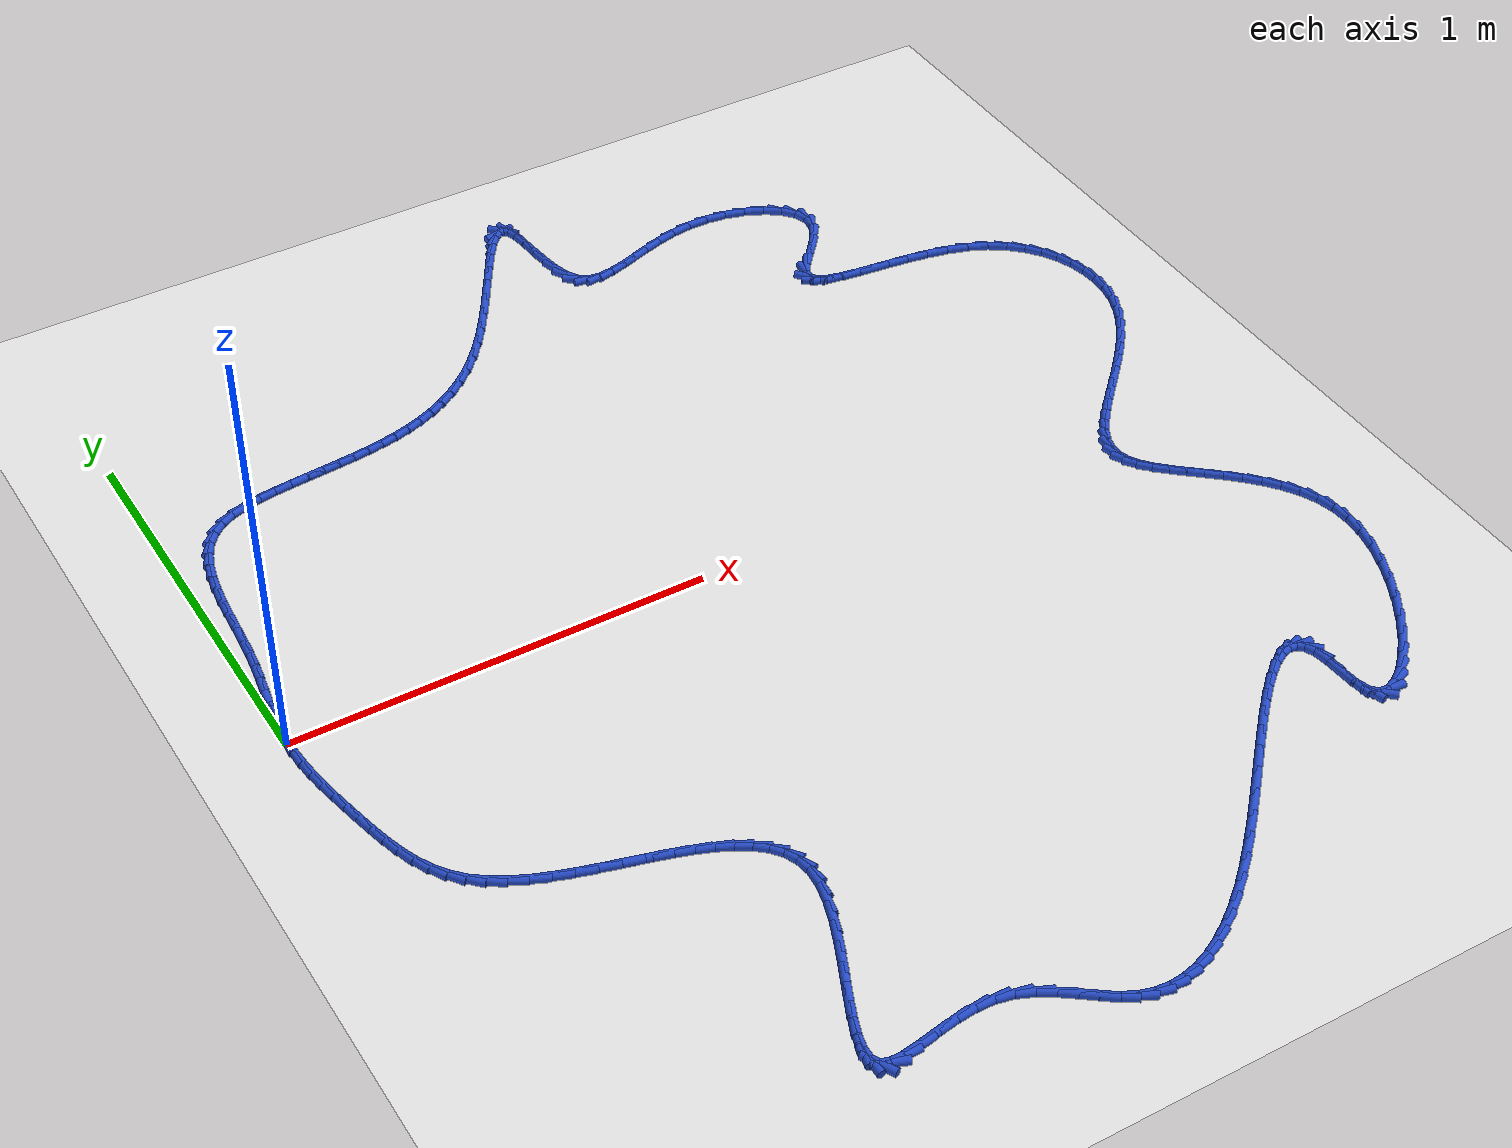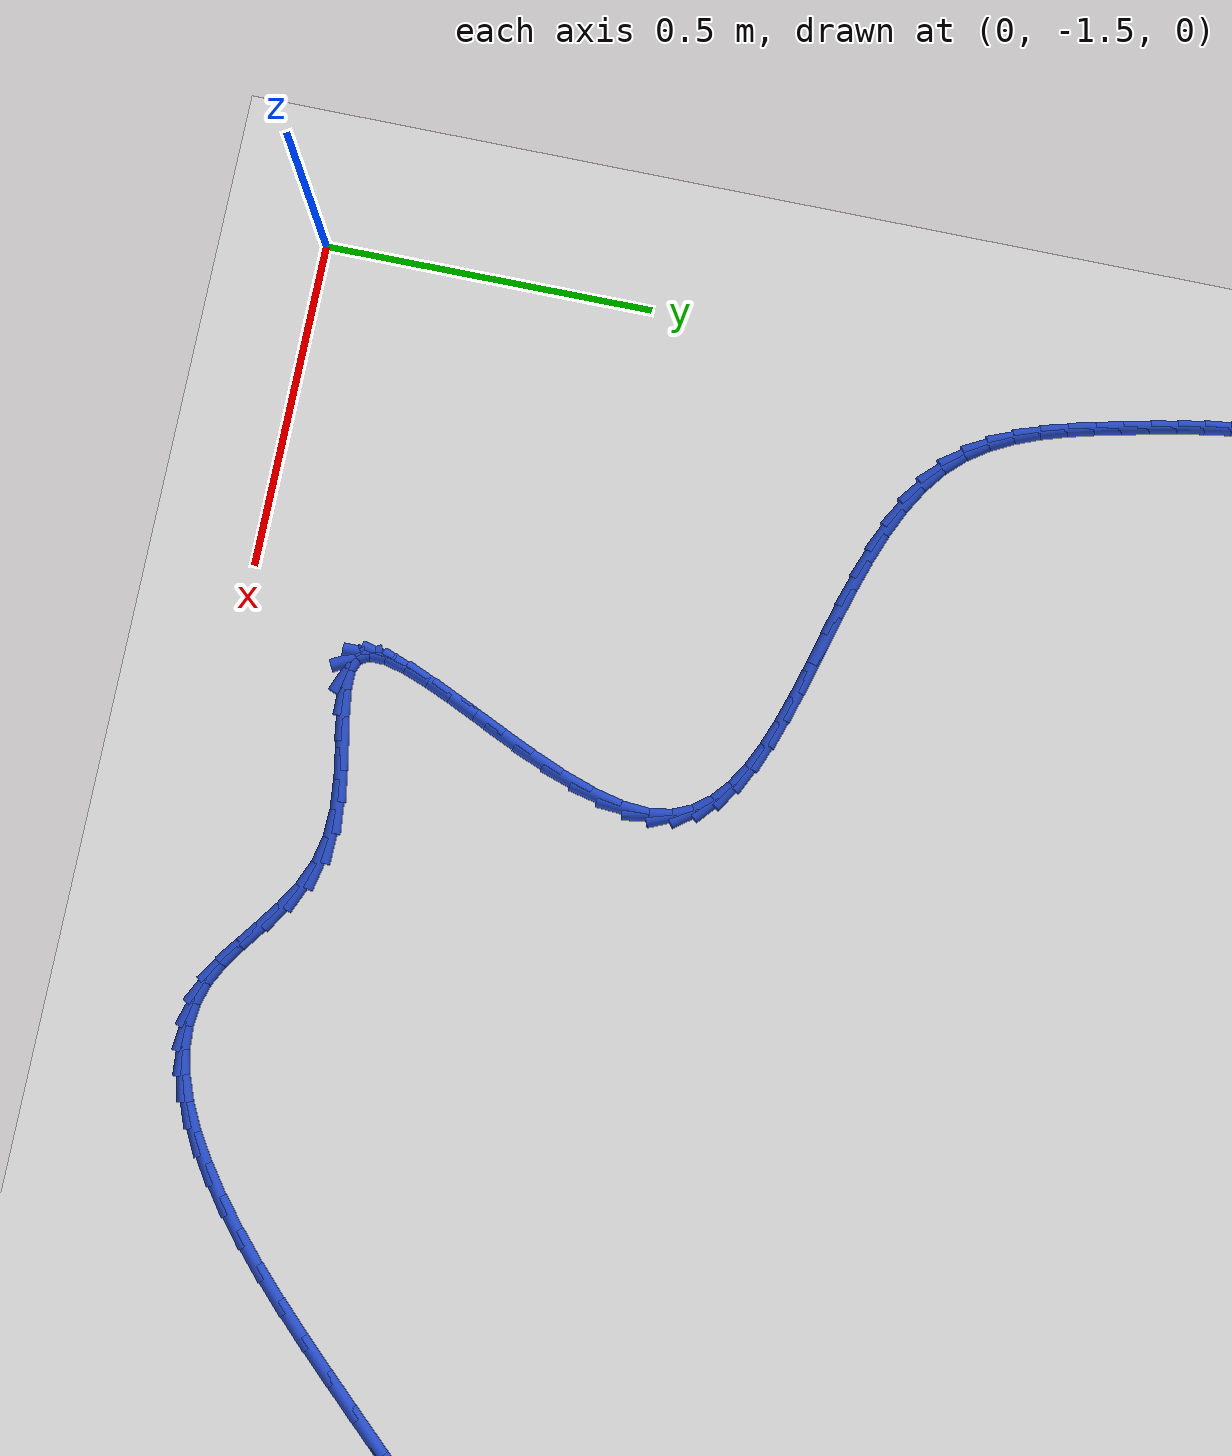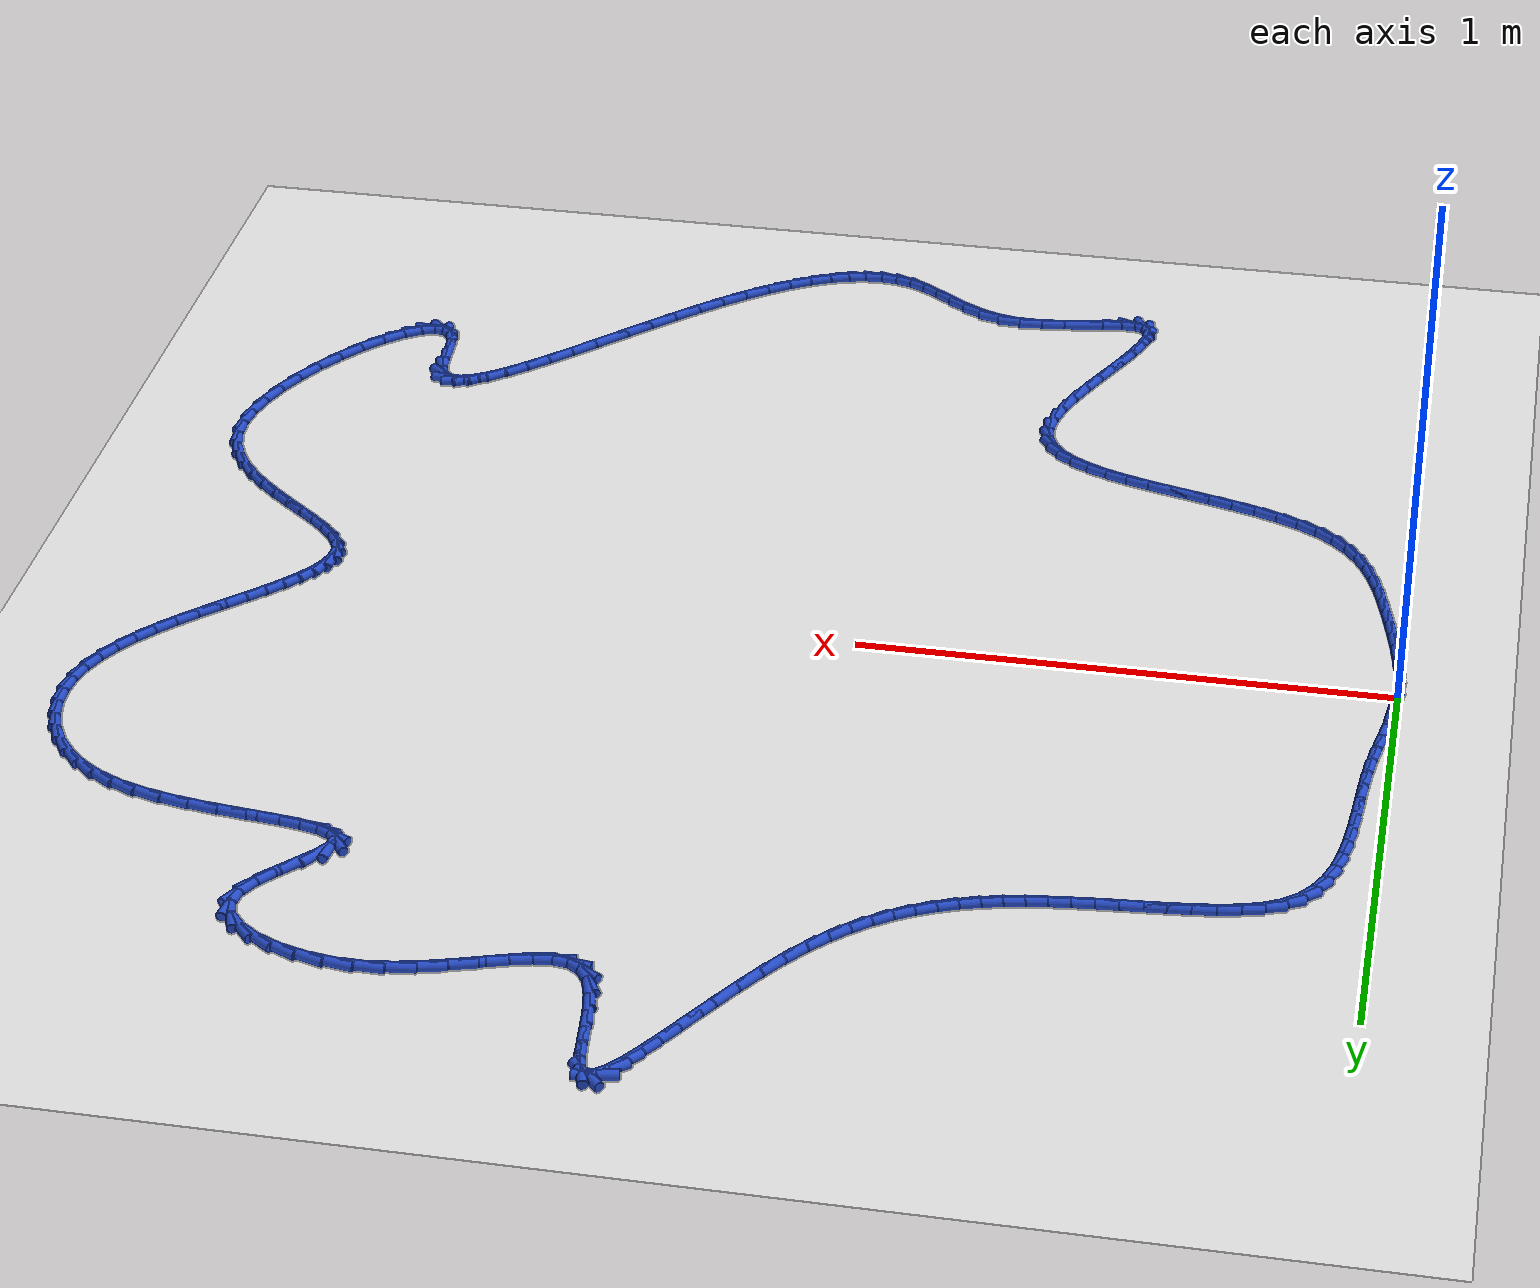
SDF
<sdf version="1.6">
 <world name="default">
  <light name="sun" type="directional">
   <pose>0 0 10 0 -0 0</pose>
   <diffuse>0.8 0.8 0.8 1</diffuse>
   <specular>0.2 0.2 0.2 1</specular>
   <attenuation>
    <range>1000</range>
    <constant>0.9</constant>
    <linear>0.01</linear>
    <quadratic>0.001</quadratic>
   </attenuation>
   <direction>-0.5 0.1 -0.9</direction>
  </light>
  <model name="ground_plane">
   <static>1</static>
   <link name="link">
    <collision name="collision">
     <geometry><plane><normal>0 0 1</normal><size>100 100</size></plane></geometry>
     <surface><friction><ode><mu>100</mu><mu2>50</mu2></ode></friction></surface>
    </collision>
    <visual name="visual">
     <cast_shadows>0</cast_shadows>
     <geometry><plane><normal>0 0 1</normal><size>100 100</size></plane></geometry>
     <material>
      <script><uri>file://media/materials/scripts/gazebo.material</uri><name>Gazebo/WhiteGlow</name></script>
     </material>
    </visual>
   </link>
  </model>
  <gravity>0 0 -9.8</gravity>
  <magnetic_field>6e-06 2.3e-05 -4.2e-05</magnetic_field>
  <atmosphere type="adiabatic"/>
  <physics name="default_physics" default="0" type="ode">
   <max_step_size>0.001</max_step_size>
   <real_time_factor>1</real_time_factor>
   <real_time_update_rate>1000</real_time_update_rate>
  </physics>
  <scene><ambient>0.4 0.4 0.4 1</ambient><background>0.7 0.7 0.7 1</background><shadows>1</shadows></scene>
  <spherical_coordinates>
   <surface_model>EARTH_WGS84</surface_model>
   <latitude_deg>0</latitude_deg>
   <longitude_deg>0</longitude_deg>
   <elevation>0</elevation>
   <heading_deg>0</heading_deg>
  </spherical_coordinates>
  <model name="line">
   <link name="link_0">
    <pose>5.204170427930421e-18 0.0 0.01 0 1.57 1.510636619257337</pose>
    <collision name="collision">
     <geometry><cylinder><radius>0.01</radius><length>0.08</length></cylinder></geometry>
    </collision>
    <visual name="visual">
     <material>
      <script><name>Gazebo/Blue</name><uri>file://media/materials/scripts/gazebo.material</uri></script>
     </material>
     <geometry><cylinder><radius>0.01</radius><length>0.08</length></cylinder></geometry>
    </visual>
   </link>
   <link name="link_1">
    <pose>0.0022938607161674084 0.0380835086436691 0.01 0 1.57 1.4565001393885795</pose>
    <collision name="collision">
     <geometry><cylinder><radius>0.01</radius><length>0.08</length></cylinder></geometry>
    </collision>
    <visual name="visual">
     <material>
      <script><name>Gazebo/Blue</name><uri>file://media/materials/scripts/gazebo.material</uri></script>
     </material>
     <geometry><cylinder><radius>0.01</radius><length>0.08</length></cylinder></geometry>
    </visual>
   </link>
   <link name="link_2">
    <pose>0.006658940441760616 0.07610800742557951 0.01 0 1.57 1.4200256374483922</pose>
    <collision name="collision">
     <geometry><cylinder><radius>0.01</radius><length>0.08</length></cylinder></geometry>
    </collision>
    <visual name="visual">
     <material>
      <script><name>Gazebo/Blue</name><uri>file://media/materials/scripts/gazebo.material</uri></script>
     </material>
     <geometry><cylinder><radius>0.01</radius><length>0.08</length></cylinder></geometry>
    </visual>
   </link>
   <link name="link_3">
    <pose>0.012472586296439016 0.11437491082924207 0.01 0 1.57 1.4013611811894124</pose>
    <collision name="collision">
     <geometry><cylinder><radius>0.01</radius><length>0.08</length></cylinder></geometry>
    </collision>
    <visual name="visual">
     <material>
      <script><name>Gazebo/Blue</name><uri>file://media/materials/scripts/gazebo.material</uri></script>
     </material>
     <geometry><cylinder><radius>0.01</radius><length>0.08</length></cylinder></geometry>
    </visual>
   </link>
   <link name="link_4">
    <pose>0.019112145399861984 0.15318563333816754 0.01 0 1.57 1.3999243317049128</pose>
    <collision name="collision">
     <geometry><cylinder><radius>0.01</radius><length>0.08</length></cylinder></geometry>
    </collision>
    <visual name="visual">
     <material>
      <script><name>Gazebo/Blue</name><uri>file://media/materials/scripts/gazebo.material</uri></script>
     </material>
     <geometry><cylinder><radius>0.01</radius><length>0.08</length></cylinder></geometry>
    </visual>
   </link>
   <link name="link_5">
    <pose>0.025954964871688923 0.19284158943586674 0.01 0 1.57 1.41465095230036</pose>
    <collision name="collision">
     <geometry><cylinder><radius>0.01</radius><length>0.08</length></cylinder></geometry>
    </collision>
    <visual name="visual">
     <material>
      <script><name>Gazebo/Blue</name><uri>file://media/materials/scripts/gazebo.material</uri></script>
     </material>
     <geometry><cylinder><radius>0.01</radius><length>0.08</length></cylinder></geometry>
    </visual>
   </link>
   <link name="link_6">
    <pose>0.032378391831579194 0.23364419360585043 0.01 0 1.57 1.4440946087735353</pose>
    <collision name="collision">
     <geometry><cylinder><radius>0.01</radius><length>0.08</length></cylinder></geometry>
    </collision>
    <visual name="visual">
     <material>
      <script><name>Gazebo/Blue</name><uri>file://media/materials/scripts/gazebo.material</uri></script>
     </material>
     <geometry><cylinder><radius>0.01</radius><length>0.08</length></cylinder></geometry>
    </visual>
   </link>
   <link name="link_7">
    <pose>0.03776039522860747 0.2758943929522019 0.01 0 1.57 1.4787377275433138</pose>
    <collision name="collision">
     <geometry><cylinder><radius>0.01</radius><length>0.08</length></cylinder></geometry>
    </collision>
    <visual name="visual">
     <material>
      <script><name>Gazebo/Blue</name><uri>file://media/materials/scripts/gazebo.material</uri></script>
     </material>
     <geometry><cylinder><radius>0.01</radius><length>0.08</length></cylinder></geometry>
    </visual>
   </link>
   <link name="link_8">
    <pose>0.041800057151947095 0.3196517795194431 0.01 0 1.57 1.4983967013484</pose>
    <collision name="collision">
     <geometry><cylinder><radius>0.01</radius><length>0.08</length></cylinder></geometry>
    </collision>
    <visual name="visual">
     <material>
      <script><name>Gazebo/Blue</name><uri>file://media/materials/scripts/gazebo.material</uri></script>
     </material>
     <geometry><cylinder><radius>0.01</radius><length>0.08</length></cylinder></geometry>
    </visual>
   </link>
   <link name="link_9">
    <pose>0.045041206233457955 0.36434101695252435 0.01 0 1.57 1.5014031646694834</pose>
    <collision name="collision">
     <geometry><cylinder><radius>0.01</radius><length>0.08</length></cylinder></geometry>
    </collision>
    <visual name="visual">
     <material>
      <script><name>Gazebo/Blue</name><uri>file://media/materials/scripts/gazebo.material</uri></script>
     </material>
     <geometry><cylinder><radius>0.01</radius><length>0.08</length></cylinder></geometry>
    </visual>
   </link>
   <link name="link_10">
    <pose>0.04816492996597125 0.4092836023907988 0.01 0 1.57 1.4881548193290182</pose>
    <collision name="collision">
     <geometry><cylinder><radius>0.01</radius><length>0.08</length></cylinder></geometry>
    </collision>
    <visual name="visual">
     <material>
      <script><name>Gazebo/Blue</name><uri>file://media/materials/scripts/gazebo.material</uri></script>
     </material>
     <geometry><cylinder><radius>0.01</radius><length>0.08</length></cylinder></geometry>
    </visual>
   </link>
   <link name="link_11">
    <pose>0.0518523158423183 0.45380103297362034 0.01 0 1.57 1.4576737201625056</pose>
    <collision name="collision">
     <geometry><cylinder><radius>0.01</radius><length>0.08</length></cylinder></geometry>
    </collision>
    <visual name="visual">
     <material>
      <script><name>Gazebo/Blue</name><uri>file://media/materials/scripts/gazebo.material</uri></script>
     </material>
     <geometry><cylinder><radius>0.01</radius><length>0.08</length></cylinder></geometry>
    </visual>
   </link>
   <link name="link_12">
    <pose>0.056784451355330334 0.4972148058403425 0.01 0 1.57 1.4075326300873543</pose>
    <collision name="collision">
     <geometry><cylinder><radius>0.01</radius><length>0.08</length></cylinder></geometry>
    </collision>
    <visual name="visual">
     <material>
      <script><name>Gazebo/Blue</name><uri>file://media/materials/scripts/gazebo.material</uri></script>
     </material>
     <geometry><cylinder><radius>0.01</radius><length>0.08</length></cylinder></geometry>
    </visual>
   </link>
   <link name="link_13">
    <pose>0.06364242399783858 0.5388464181303186 0.01 0 1.57 1.3337101877858397</pose>
    <collision name="collision">
     <geometry><cylinder><radius>0.01</radius><length>0.08</length></cylinder></geometry>
    </collision>
    <visual name="visual">
     <material>
      <script><name>Gazebo/Blue</name><uri>file://media/materials/scripts/gazebo.material</uri></script>
     </material>
     <geometry><cylinder><radius>0.01</radius><length>0.08</length></cylinder></geometry>
    </visual>
   </link>
   <link name="link_14">
    <pose>0.07310732126267436 0.578017366982903 0.01 0 1.57 1.2306202392710377</pose>
    <collision name="collision">
     <geometry><cylinder><radius>0.01</radius><length>0.08</length></cylinder></geometry>
    </collision>
    <visual name="visual">
     <material>
      <script><name>Gazebo/Blue</name><uri>file://media/materials/scripts/gazebo.material</uri></script>
     </material>
     <geometry><cylinder><radius>0.01</radius><length>0.08</length></cylinder></geometry>
    </visual>
   </link>
   <link name="link_15">
    <pose>0.08586023064266884 0.6140491495374485 0.01 0 1.57 1.0919939815067272</pose>
    <collision name="collision">
     <geometry><cylinder><radius>0.01</radius><length>0.08</length></cylinder></geometry>
    </collision>
    <visual name="visual">
     <material>
      <script><name>Gazebo/Blue</name><uri>file://media/materials/scripts/gazebo.material</uri></script>
     </material>
     <geometry><cylinder><radius>0.01</radius><length>0.08</length></cylinder></geometry>
    </visual>
   </link>
   <link name="link_16">
    <pose>0.10258223963065338 0.6462632629333089 0.01 0 1.57 0.9139524919822724</pose>
    <collision name="collision">
     <geometry><cylinder><radius>0.01</radius><length>0.08</length></cylinder></geometry>
    </collision>
    <visual name="visual">
     <material>
      <script><name>Gazebo/Blue</name><uri>file://media/materials/scripts/gazebo.material</uri></script>
     </material>
     <geometry><cylinder><radius>0.01</radius><length>0.08</length></cylinder></geometry>
    </visual>
   </link>
   <link name="link_17">
    <pose>0.12395443571945916 0.673981204309838 0.01 0 1.57 0.7011252617028481</pose>
    <collision name="collision">
     <geometry><cylinder><radius>0.01</radius><length>0.08</length></cylinder></geometry>
    </collision>
    <visual name="visual">
     <material>
      <script><name>Gazebo/Blue</name><uri>file://media/materials/scripts/gazebo.material</uri></script>
     </material>
     <geometry><cylinder><radius>0.01</radius><length>0.08</length></cylinder></geometry>
    </visual>
   </link>
   <link name="link_18">
    <pose>0.15065780450031493 0.6965245563262074 0.01 0 1.57 0.48530061039437883</pose>
    <collision name="collision">
     <geometry><cylinder><radius>0.01</radius><length>0.08</length></cylinder></geometry>
    </collision>
    <visual name="visual">
     <material>
      <script><name>Gazebo/Blue</name><uri>file://media/materials/scripts/gazebo.material</uri></script>
     </material>
     <geometry><cylinder><radius>0.01</radius><length>0.08</length></cylinder></geometry>
    </visual>
   </link>
   <link name="link_19">
    <pose>0.18296155376172307 0.7135604817101712 0.01 0 1.57 0.3230330626207582</pose>
    <collision name="collision">
     <geometry><cylinder><radius>0.01</radius><length>0.08</length></cylinder></geometry>
    </collision>
    <visual name="visual">
     <material>
      <script><name>Gazebo/Blue</name><uri>file://media/materials/scripts/gazebo.material</uri></script>
     </material>
     <geometry><cylinder><radius>0.01</radius><length>0.08</length></cylinder></geometry>
    </visual>
   </link>
   <link name="link_20">
    <pose>0.21978633292603755 0.7258879062169596 0.01 0 1.57 0.21299831055828786</pose>
    <collision name="collision">
     <geometry><cylinder><radius>0.01</radius><length>0.08</length></cylinder></geometry>
    </collision>
    <visual name="visual">
     <material>
      <script><name>Gazebo/Blue</name><uri>file://media/materials/scripts/gazebo.material</uri></script>
     </material>
     <geometry><cylinder><radius>0.01</radius><length>0.08</length></cylinder></geometry>
    </visual>
   </link>
   <link name="link_21">
    <pose>0.2597771550120717 0.7345370804731506 0.01 0 1.57 0.1425880608667658</pose>
    <collision name="collision">
     <geometry><cylinder><radius>0.01</radius><length>0.08</length></cylinder></geometry>
    </collision>
    <visual name="visual">
     <material>
      <script><name>Gazebo/Blue</name><uri>file://media/materials/scripts/gazebo.material</uri></script>
     </material>
     <geometry><cylinder><radius>0.01</radius><length>0.08</length></cylinder></geometry>
    </visual>
   </link>
   <link name="link_22">
    <pose>0.301579033038639 0.7405382551053217 0.01 0 1.57 0.10335853625218103</pose>
    <collision name="collision">
     <geometry><cylinder><radius>0.01</radius><length>0.08</length></cylinder></geometry>
    </collision>
    <visual name="visual">
     <material>
      <script><name>Gazebo/Blue</name><uri>file://media/materials/scripts/gazebo.material</uri></script>
     </material>
     <geometry><cylinder><radius>0.01</radius><length>0.08</length></cylinder></geometry>
    </visual>
   </link>
   <link name="link_23">
    <pose>0.34383712811158723 0.7449216101934814 0.01 0 1.57 0.08753427483744719</pose>
    <collision name="collision">
     <geometry><cylinder><radius>0.01</radius><length>0.08</length></cylinder></geometry>
    </collision>
    <visual name="visual">
     <material>
      <script><name>Gazebo/Blue</name><uri>file://media/materials/scripts/gazebo.material</uri></script>
     </material>
     <geometry><cylinder><radius>0.01</radius><length>0.08</length></cylinder></geometry>
    </visual>
   </link>
   <link name="link_24">
    <pose>0.3854909745000385 0.748577090604662 0.01 0 1.57 0.08254679387309169</pose>
    <collision name="collision">
     <geometry><cylinder><radius>0.01</radius><length>0.08</length></cylinder></geometry>
    </collision>
    <visual name="visual">
     <material>
      <script><name>Gazebo/Blue</name><uri>file://media/materials/scripts/gazebo.material</uri></script>
     </material>
     <geometry><cylinder><radius>0.01</radius><length>0.08</length></cylinder></geometry>
    </visual>
   </link>
   <link name="link_25">
    <pose>0.42639056807646664 0.7519609101706646 0.01 0 1.57 0.08653233254181558</pose>
    <collision name="collision">
     <geometry><cylinder><radius>0.01</radius><length>0.08</length></cylinder></geometry>
    </collision>
    <visual name="visual">
     <material>
      <script><name>Gazebo/Blue</name><uri>file://media/materials/scripts/gazebo.material</uri></script>
     </material>
     <geometry><cylinder><radius>0.01</radius><length>0.08</length></cylinder></geometry>
    </visual>
   </link>
   <link name="link_26">
    <pose>0.46656138423578275 0.755445686759826 0.01 0 1.57 0.09995964827615168</pose>
    <collision name="collision">
     <geometry><cylinder><radius>0.01</radius><length>0.08</length></cylinder></geometry>
    </collision>
    <visual name="visual">
     <material>
      <script><name>Gazebo/Blue</name><uri>file://media/materials/scripts/gazebo.material</uri></script>
     </material>
     <geometry><cylinder><radius>0.01</radius><length>0.08</length></cylinder></geometry>
    </visual>
   </link>
   <link name="link_27">
    <pose>0.5060288983728978 0.7594040382404825 0.01 0 1.57 0.12323373551644948</pose>
    <collision name="collision">
     <geometry><cylinder><radius>0.01</radius><length>0.08</length></cylinder></geometry>
    </collision>
    <visual name="visual">
     <material>
      <script><name>Gazebo/Blue</name><uri>file://media/materials/scripts/gazebo.material</uri></script>
     </material>
     <geometry><cylinder><radius>0.01</radius><length>0.08</length></cylinder></geometry>
    </visual>
   </link>
   <link name="link_28">
    <pose>0.5448185858827226 0.7642085824809711 0.01 0 1.57 0.15664460560736038</pose>
    <collision name="collision">
     <geometry><cylinder><radius>0.01</radius><length>0.08</length></cylinder></geometry>
    </collision>
    <visual name="visual">
     <material>
      <script><name>Gazebo/Blue</name><uri>file://media/materials/scripts/gazebo.material</uri></script>
     </material>
     <geometry><cylinder><radius>0.01</radius><length>0.08</length></cylinder></geometry>
    </visual>
   </link>
   <link name="link_29">
    <pose>0.582955922160168 0.7702319373496286 0.01 0 1.57 0.2002825979933182</pose>
    <collision name="collision">
     <geometry><cylinder><radius>0.01</radius><length>0.08</length></cylinder></geometry>
    </collision>
    <visual name="visual">
     <material>
      <script><name>Gazebo/Blue</name><uri>file://media/materials/scripts/gazebo.material</uri></script>
     </material>
     <geometry><cylinder><radius>0.01</radius><length>0.08</length></cylinder></geometry>
    </visual>
   </link>
   <link name="link_30">
    <pose>0.6204663826001451 0.7778467207147917 0.01 0 1.57 0.25392323454841886</pose>
    <collision name="collision">
     <geometry><cylinder><radius>0.01</radius><length>0.08</length></cylinder></geometry>
    </collision>
    <visual name="visual">
     <material>
      <script><name>Gazebo/Blue</name><uri>file://media/materials/scripts/gazebo.material</uri></script>
     </material>
     <geometry><cylinder><radius>0.01</radius><length>0.08</length></cylinder></geometry>
    </visual>
   </link>
   <link name="link_31">
    <pose>0.657375442597565 0.7874255504447971 0.01 0 1.57 0.3168988077317452</pose>
    <collision name="collision">
     <geometry><cylinder><radius>0.01</radius><length>0.08</length></cylinder></geometry>
    </collision>
    <visual name="visual">
     <material>
      <script><name>Gazebo/Blue</name><uri>file://media/materials/scripts/gazebo.material</uri></script>
     </material>
     <geometry><cylinder><radius>0.01</radius><length>0.08</length></cylinder></geometry>
    </visual>
   </link>
   <link name="link_32">
    <pose>0.6937085775473385 0.7993410444079817 0.01 0 1.57 0.38799320603928406</pose>
    <collision name="collision">
     <geometry><cylinder><radius>0.01</radius><length>0.08</length></cylinder></geometry>
    </collision>
    <visual name="visual">
     <material>
      <script><name>Gazebo/Blue</name><uri>file://media/materials/scripts/gazebo.material</uri></script>
     </material>
     <geometry><cylinder><radius>0.01</radius><length>0.08</length></cylinder></geometry>
    </visual>
   </link>
   <link name="link_33">
    <pose>0.7294912628443764 0.813965820472682 0.01 0 1.57 0.4654118026864059</pose>
    <collision name="collision">
     <geometry><cylinder><radius>0.01</radius><length>0.08</length></cylinder></geometry>
    </collision>
    <visual name="visual">
     <material>
      <script><name>Gazebo/Blue</name><uri>file://media/materials/scripts/gazebo.material</uri></script>
     </material>
     <geometry><cylinder><radius>0.01</radius><length>0.08</length></cylinder></geometry>
    </visual>
   </link>
   <link name="link_34">
    <pose>0.76474897388359 0.8316724965072351 0.01 0 1.57 0.5468732517467415</pose>
    <collision name="collision">
     <geometry><cylinder><radius>0.01</radius><length>0.08</length></cylinder></geometry>
    </collision>
    <visual name="visual">
     <material>
      <script><name>Gazebo/Blue</name><uri>file://media/materials/scripts/gazebo.material</uri></script>
     </material>
     <geometry><cylinder><radius>0.01</radius><length>0.08</length></cylinder></geometry>
    </visual>
   </link>
   <link name="link_35">
    <pose>0.79950718605989 0.8528336903799779 0.01 0 1.57 0.6298328229557189</pose>
    <collision name="collision">
     <geometry><cylinder><radius>0.01</radius><length>0.08</length></cylinder></geometry>
    </collision>
    <visual name="visual">
     <material>
      <script><name>Gazebo/Blue</name><uri>file://media/materials/scripts/gazebo.material</uri></script>
     </material>
     <geometry><cylinder><radius>0.01</radius><length>0.08</length></cylinder></geometry>
    </visual>
   </link>
   <link name="link_36">
    <pose>0.8337913747681874 0.8778220199592466 0.01 0 1.57 0.7117884166552221</pose>
    <collision name="collision">
     <geometry><cylinder><radius>0.01</radius><length>0.08</length></cylinder></geometry>
    </collision>
    <visual name="visual">
     <material>
      <script><name>Gazebo/Blue</name><uri>file://media/materials/scripts/gazebo.material</uri></script>
     </material>
     <geometry><cylinder><radius>0.01</radius><length>0.08</length></cylinder></geometry>
    </visual>
   </link>
   <link name="link_37">
    <pose>0.867627015403393 0.9070101031133782 0.01 0 1.57 0.7905770807191329</pose>
    <collision name="collision">
     <geometry><cylinder><radius>0.01</radius><length>0.08</length></cylinder></geometry>
    </collision>
    <visual name="visual">
     <material>
      <script><name>Gazebo/Blue</name><uri>file://media/materials/scripts/gazebo.material</uri></script>
     </material>
     <geometry><cylinder><radius>0.01</radius><length>0.08</length></cylinder></geometry>
    </visual>
   </link>
   <link name="link_38">
    <pose>0.901039583360418 0.9407705577107093 0.01 0 1.57 0.8645747442121784</pose>
    <collision name="collision">
     <geometry><cylinder><radius>0.01</radius><length>0.08</length></cylinder></geometry>
    </collision>
    <visual name="visual">
     <material>
      <script><name>Gazebo/Blue</name><uri>file://media/materials/scripts/gazebo.material</uri></script>
     </material>
     <geometry><cylinder><radius>0.01</radius><length>0.08</length></cylinder></geometry>
    </visual>
   </link>
   <link name="link_39">
    <pose>0.9340545540341735 0.9794760016195772 0.01 0 1.57 0.9299229409245141</pose>
    <collision name="collision">
     <geometry><cylinder><radius>0.01</radius><length>0.08</length></cylinder></geometry>
    </collision>
    <visual name="visual">
     <material>
      <script><name>Gazebo/Blue</name><uri>file://media/materials/scripts/gazebo.material</uri></script>
     </material>
     <geometry><cylinder><radius>0.01</radius><length>0.08</length></cylinder></geometry>
    </visual>
   </link>
   <link name="link_40">
    <pose>0.966652335631667 1.0231784862646711 0.01 0 1.57 0.9770418076062122</pose>
    <collision name="collision">
     <geometry><cylinder><radius>0.01</radius><length>0.08</length></cylinder></geometry>
    </collision>
    <visual name="visual">
     <material>
      <script><name>Gazebo/Blue</name><uri>file://media/materials/scripts/gazebo.material</uri></script>
     </material>
     <geometry><cylinder><radius>0.01</radius><length>0.08</length></cylinder></geometry>
    </visual>
   </link>
   <link name="link_41">
    <pose>0.9986169186587432 1.0705329285508542 0.01 0 1.57 1.0083919957232428</pose>
    <collision name="collision">
     <geometry><cylinder><radius>0.01</radius><length>0.08</length></cylinder></geometry>
    </collision>
    <visual name="visual">
     <material>
      <script><name>Gazebo/Blue</name><uri>file://media/materials/scripts/gazebo.material</uri></script>
     </material>
     <geometry><cylinder><radius>0.01</radius><length>0.08</length></cylinder></geometry>
    </visual>
   </link>
   <link name="link_42">
    <pose>1.0296787967351808 1.119813717834889 0.01 0 1.57 1.0273989495254094</pose>
    <collision name="collision">
     <geometry><cylinder><radius>0.01</radius><length>0.08</length></cylinder></geometry>
    </collision>
    <visual name="visual">
     <material>
      <script><name>Gazebo/Blue</name><uri>file://media/materials/scripts/gazebo.material</uri></script>
     </material>
     <geometry><cylinder><radius>0.01</radius><length>0.08</length></cylinder></geometry>
    </visual>
   </link>
   <link name="link_43">
    <pose>1.0595684623324828 1.1692952353057666 0.01 0 1.57 1.0353906798098473</pose>
    <collision name="collision">
     <geometry><cylinder><radius>0.01</radius><length>0.08</length></cylinder></geometry>
    </collision>
    <visual name="visual">
     <material>
      <script><name>Gazebo/Blue</name><uri>file://media/materials/scripts/gazebo.material</uri></script>
     </material>
     <geometry><cylinder><radius>0.01</radius><length>0.08</length></cylinder></geometry>
    </visual>
   </link>
   <link name="link_44">
    <pose>1.0880164079221522 1.2172518621524775 0.01 0 1.57 1.031808184294277</pose>
    <collision name="collision">
     <geometry><cylinder><radius>0.01</radius><length>0.08</length></cylinder></geometry>
    </collision>
    <visual name="visual">
     <material>
      <script><name>Gazebo/Blue</name><uri>file://media/materials/scripts/gazebo.material</uri></script>
     </material>
     <geometry><cylinder><radius>0.01</radius><length>0.08</length></cylinder></geometry>
    </visual>
   </link>
   <link name="link_45">
    <pose>1.1147531259756915 1.2619579795640128 0.01 0 1.57 1.0135603595255736</pose>
    <collision name="collision">
     <geometry><cylinder><radius>0.01</radius><length>0.08</length></cylinder></geometry>
    </collision>
    <visual name="visual">
     <material>
      <script><name>Gazebo/Blue</name><uri>file://media/materials/scripts/gazebo.material</uri></script>
     </material>
     <geometry><cylinder><radius>0.01</radius><length>0.08</length></cylinder></geometry>
    </visual>
   </link>
   <link name="link_46">
    <pose>1.139509108964605 1.3016879687293639 0.01 0 1.57 0.9726568364648543</pose>
    <collision name="collision">
     <geometry><cylinder><radius>0.01</radius><length>0.08</length></cylinder></geometry>
    </collision>
    <visual name="visual">
     <material>
      <script><name>Gazebo/Blue</name><uri>file://media/materials/scripts/gazebo.material</uri></script>
     </material>
     <geometry><cylinder><radius>0.01</radius><length>0.08</length></cylinder></geometry>
    </visual>
   </link>
   <link name="link_47">
    <pose>1.1620148493603948 1.3347162108375208 0.01 0 1.57 0.8885341719777671</pose>
    <collision name="collision">
     <geometry><cylinder><radius>0.01</radius><length>0.08</length></cylinder></geometry>
    </collision>
    <visual name="visual">
     <material>
      <script><name>Gazebo/Blue</name><uri>file://media/materials/scripts/gazebo.material</uri></script>
     </material>
     <geometry><cylinder><radius>0.01</radius><length>0.08</length></cylinder></geometry>
    </visual>
   </link>
   <link name="link_48">
    <pose>1.1820008396345643 1.3593170870774745 0.01 0 1.57 0.6987496948332145</pose>
    <collision name="collision">
     <geometry><cylinder><radius>0.01</radius><length>0.08</length></cylinder></geometry>
    </collision>
    <visual name="visual">
     <material>
      <script><name>Gazebo/Blue</name><uri>file://media/materials/scripts/gazebo.material</uri></script>
     </material>
     <geometry><cylinder><radius>0.01</radius><length>0.08</length></cylinder></geometry>
    </visual>
   </link>
   <link name="link_49">
    <pose>1.1991975722586163 1.3737649786382164 0.01 0 1.57 0.17976781300560304</pose>
    <collision name="collision">
     <geometry><cylinder><radius>0.01</radius><length>0.08</length></cylinder></geometry>
    </collision>
    <visual name="visual">
     <material>
      <script><name>Gazebo/Blue</name><uri>file://media/materials/scripts/gazebo.material</uri></script>
     </material>
     <geometry><cylinder><radius>0.01</radius><length>0.08</length></cylinder></geometry>
    </visual>
   </link>
   <link name="link_50">
    <pose>1.2133355397040542 1.376334266708737 0.01 0 1.57 -0.7957087761802857</pose>
    <collision name="collision">
     <geometry><cylinder><radius>0.01</radius><length>0.08</length></cylinder></geometry>
    </collision>
    <visual name="visual">
     <material>
      <script><name>Gazebo/Blue</name><uri>file://media/materials/scripts/gazebo.material</uri></script>
     </material>
     <geometry><cylinder><radius>0.01</radius><length>0.08</length></cylinder></geometry>
    </visual>
   </link>
   <link name="link_51">
    <pose>1.2241452344423807 1.3652993324780276 0.01 0 1.57 -1.2891943024898151</pose>
    <collision name="collision">
     <geometry><cylinder><radius>0.01</radius><length>0.08</length></cylinder></geometry>
    </collision>
    <visual name="visual">
     <material>
      <script><name>Gazebo/Blue</name><uri>file://media/materials/scripts/gazebo.material</uri></script>
     </material>
     <geometry><cylinder><radius>0.01</radius><length>0.08</length></cylinder></geometry>
    </visual>
   </link>
   <link name="link_52">
    <pose>1.231565157312084 1.339650562524224 0.01 0 1.57 -1.4331246955087147</pose>
    <collision name="collision">
     <geometry><cylinder><radius>0.01</radius><length>0.08</length></cylinder></geometry>
    </collision>
    <visual name="visual">
     <material>
      <script><name>Gazebo/Blue</name><uri>file://media/materials/scripts/gazebo.material</uri></script>
     </material>
     <geometry><cylinder><radius>0.01</radius><length>0.08</length></cylinder></geometry>
    </visual>
   </link>
   <link name="link_53">
    <pose>1.2367184004669716 1.3024559378895586 0.01 0 1.57 -1.4710093863283586</pose>
    <collision name="collision">
     <geometry><cylinder><radius>0.01</radius><length>0.08</length></cylinder></geometry>
    </collision>
    <visual name="visual">
     <material>
      <script><name>Gazebo/Blue</name><uri>file://media/materials/scripts/gazebo.material</uri></script>
     </material>
     <geometry><cylinder><radius>0.01</radius><length>0.08</length></cylinder></geometry>
    </visual>
   </link>
   <link name="link_54">
    <pose>1.2411467961692795 1.2582248247808703 0.01 0 1.57 -1.4590683940083717</pose>
    <collision name="collision">
     <geometry><cylinder><radius>0.01</radius><length>0.08</length></cylinder></geometry>
    </collision>
    <visual name="visual">
     <material>
      <script><name>Gazebo/Blue</name><uri>file://media/materials/scripts/gazebo.material</uri></script>
     </material>
     <geometry><cylinder><radius>0.01</radius><length>0.08</length></cylinder></geometry>
    </visual>
   </link>
   <link name="link_55">
    <pose>1.2463926583519807 1.2114682474096663 0.01 0 1.57 -1.4025240571177398</pose>
    <collision name="collision">
     <geometry><cylinder><radius>0.01</radius><length>0.08</length></cylinder></geometry>
    </collision>
    <visual name="visual">
     <material>
      <script><name>Gazebo/Blue</name><uri>file://media/materials/scripts/gazebo.material</uri></script>
     </material>
     <geometry><cylinder><radius>0.01</radius><length>0.08</length></cylinder></geometry>
    </visual>
   </link>
   <link name="link_56">
    <pose>1.2539983009480475 1.1666972299874532 0.01 0 1.57 -1.2787306433403571</pose>
    <collision name="collision">
     <geometry><cylinder><radius>0.01</radius><length>0.08</length></cylinder></geometry>
    </collision>
    <visual name="visual">
     <material>
      <script><name>Gazebo/Blue</name><uri>file://media/materials/scripts/gazebo.material</uri></script>
     </material>
     <geometry><cylinder><radius>0.01</radius><length>0.08</length></cylinder></geometry>
    </visual>
   </link>
   <link name="link_57">
    <pose>1.2655060378904543 1.1284227967257388 0.01 0 1.57 -1.0163500280013995</pose>
    <collision name="collision">
     <geometry><cylinder><radius>0.01</radius><length>0.08</length></cylinder></geometry>
    </collision>
    <visual name="visual">
     <material>
      <script><name>Gazebo/Blue</name><uri>file://media/materials/scripts/gazebo.material</uri></script>
     </material>
     <geometry><cylinder><radius>0.01</radius><length>0.08</length></cylinder></geometry>
    </visual>
   </link>
   <link name="link_58">
    <pose>1.2824356260562149 1.1010834803385525 0.01 0 1.57 -0.5710843468272183</pose>
    <collision name="collision">
     <geometry><cylinder><radius>0.01</radius><length>0.08</length></cylinder></geometry>
    </collision>
    <visual name="visual">
     <material>
      <script><name>Gazebo/Blue</name><uri>file://media/materials/scripts/gazebo.material</uri></script>
     </material>
     <geometry><cylinder><radius>0.01</radius><length>0.08</length></cylinder></geometry>
    </visual>
   </link>
   <link name="link_59">
    <pose>1.3054324981939296 1.0863080024783072 0.01 0 1.57 -0.14689999187408434</pose>
    <collision name="collision">
     <geometry><cylinder><radius>0.01</radius><length>0.08</length></cylinder></geometry>
    </collision>
    <visual name="visual">
     <material>
      <script><name>Gazebo/Blue</name><uri>file://media/materials/scripts/gazebo.material</uri></script>
     </material>
     <geometry><cylinder><radius>0.01</radius><length>0.08</length></cylinder></geometry>
    </visual>
   </link>
   <link name="link_60">
    <pose>1.3340078002253346 1.0820798329170298 0.01 0 1.57 0.12027306153641136</pose>
    <collision name="collision">
     <geometry><cylinder><radius>0.01</radius><length>0.08</length></cylinder></geometry>
    </collision>
    <visual name="visual">
     <material>
      <script><name>Gazebo/Blue</name><uri>file://media/materials/scripts/gazebo.material</uri></script>
     </material>
     <geometry><cylinder><radius>0.01</radius><length>0.08</length></cylinder></geometry>
    </visual>
   </link>
   <link name="link_61">
    <pose>1.367597021584127 1.0861393045509935 0.01 0 1.57 0.2592227981467404</pose>
    <collision name="collision">
     <geometry><cylinder><radius>0.01</radius><length>0.08</length></cylinder></geometry>
    </collision>
    <visual name="visual">
     <material>
      <script><name>Gazebo/Blue</name><uri>file://media/materials/scripts/gazebo.material</uri></script>
     </material>
     <geometry><cylinder><radius>0.01</radius><length>0.08</length></cylinder></geometry>
    </visual>
   </link>
   <link name="link_62">
    <pose>1.4056356517040018 1.0962267502764715 0.01 0 1.57 0.3191989627151932</pose>
    <collision name="collision">
     <geometry><cylinder><radius>0.01</radius><length>0.08</length></cylinder></geometry>
    </collision>
    <visual name="visual">
     <material>
      <script><name>Gazebo/Blue</name><uri>file://media/materials/scripts/gazebo.material</uri></script>
     </material>
     <geometry><cylinder><radius>0.01</radius><length>0.08</length></cylinder></geometry>
    </visual>
   </link>
   <link name="link_63">
    <pose>1.4475591800186558 1.110082502989737 0.01 0 1.57 0.32737116722858617</pose>
    <collision name="collision">
     <geometry><cylinder><radius>0.01</radius><length>0.08</length></cylinder></geometry>
    </collision>
    <visual name="visual">
     <material>
      <script><name>Gazebo/Blue</name><uri>file://media/materials/scripts/gazebo.material</uri></script>
     </material>
     <geometry><cylinder><radius>0.01</radius><length>0.08</length></cylinder></geometry>
    </visual>
   </link>
   <link name="link_64">
    <pose>1.4928030959617844 1.1254468955870633 0.01 0 1.57 0.29553107477926754</pose>
    <collision name="collision">
     <geometry><cylinder><radius>0.01</radius><length>0.08</length></cylinder></geometry>
    </collision>
    <visual name="visual">
     <material>
      <script><name>Gazebo/Blue</name><uri>file://media/materials/scripts/gazebo.material</uri></script>
     </material>
     <geometry><cylinder><radius>0.01</radius><length>0.08</length></cylinder></geometry>
    </visual>
   </link>
   <link name="link_65">
    <pose>1.5408028889670844 1.1400602609647243 0.01 0 1.57 0.22717895545561914</pose>
    <collision name="collision">
     <geometry><cylinder><radius>0.01</radius><length>0.08</length></cylinder></geometry>
    </collision>
    <visual name="visual">
     <material>
      <script><name>Gazebo/Blue</name><uri>file://media/materials/scripts/gazebo.material</uri></script>
     </material>
     <geometry><cylinder><radius>0.01</radius><length>0.08</length></cylinder></geometry>
    </visual>
   </link>
   <link name="link_66">
    <pose>1.5909940484682528 1.151662932018993 0.01 0 1.57 0.12159994487263455</pose>
    <collision name="collision">
     <geometry><cylinder><radius>0.01</radius><length>0.08</length></cylinder></geometry>
    </collision>
    <visual name="visual">
     <material>
      <script><name>Gazebo/Blue</name><uri>file://media/materials/scripts/gazebo.material</uri></script>
     </material>
     <geometry><cylinder><radius>0.01</radius><length>0.08</length></cylinder></geometry>
    </visual>
   </link>
   <link name="link_67">
    <pose>1.6428120638989832 1.1579952416461425 0.01 0 1.57 -0.017429583581696672</pose>
    <collision name="collision">
     <geometry><cylinder><radius>0.01</radius><length>0.08</length></cylinder></geometry>
    </collision>
    <visual name="visual">
     <material>
      <script><name>Gazebo/Blue</name><uri>file://media/materials/scripts/gazebo.material</uri></script>
     </material>
     <geometry><cylinder><radius>0.01</radius><length>0.08</length></cylinder></geometry>
    </visual>
   </link>
   <link name="link_68">
    <pose>1.6955278284254984 1.157076334768679 0.01 0 1.57 -0.15701295126049303</pose>
    <collision name="collision">
     <geometry><cylinder><radius>0.01</radius><length>0.08</length></cylinder></geometry>
    </collision>
    <visual name="visual">
     <material>
      <script><name>Gazebo/Blue</name><uri>file://media/materials/scripts/gazebo.material</uri></script>
     </material>
     <geometry><cylinder><radius>0.01</radius><length>0.08</length></cylinder></geometry>
    </visual>
   </link>
   <link name="link_69">
    <pose>1.747254037895647 1.148887243696133 0.01 0 1.57 -0.2939301334624299</pose>
    <collision name="collision">
     <geometry><cylinder><radius>0.01</radius><length>0.08</length></cylinder></geometry>
    </collision>
    <visual name="visual">
     <material>
      <script><name>Gazebo/Blue</name><uri>file://media/materials/scripts/gazebo.material</uri></script>
     </material>
     <geometry><cylinder><radius>0.01</radius><length>0.08</length></cylinder></geometry>
    </visual>
   </link>
   <link name="link_70">
    <pose>1.7956062370420536 1.1342511322875855 0.01 0 1.57 -0.4439389136432677</pose>
    <collision name="collision">
     <geometry><cylinder><radius>0.01</radius><length>0.08</length></cylinder></geometry>
    </collision>
    <visual name="visual">
     <material>
      <script><name>Gazebo/Blue</name><uri>file://media/materials/scripts/gazebo.material</uri></script>
     </material>
     <geometry><cylinder><radius>0.01</radius><length>0.08</length></cylinder></geometry>
    </visual>
   </link>
   <link name="link_71">
    <pose>1.8381980594227822 1.1139944017686734 0.01 0 1.57 -0.6287959395421302</pose>
    <collision name="collision">
     <geometry><cylinder><radius>0.01</radius><length>0.08</length></cylinder></geometry>
    </collision>
    <visual name="visual">
     <material>
      <script><name>Gazebo/Blue</name><uri>file://media/materials/scripts/gazebo.material</uri></script>
     </material>
     <geometry><cylinder><radius>0.01</radius><length>0.08</length></cylinder></geometry>
    </visual>
   </link>
   <link name="link_72">
    <pose>1.8726431385958988 1.0889434533650344 0.01 0 1.57 -0.8815811827319583</pose>
    <collision name="collision">
     <geometry><cylinder><radius>0.01</radius><length>0.08</length></cylinder></geometry>
    </collision>
    <visual name="visual">
     <material>
      <script><name>Gazebo/Blue</name><uri>file://media/materials/scripts/gazebo.material</uri></script>
     </material>
     <geometry><cylinder><radius>0.01</radius><length>0.08</length></cylinder></geometry>
    </visual>
   </link>
   <link name="link_73">
    <pose>1.8965551081194667 1.0599246883023061 0.01 0 1.57 -1.2414412226056262</pose>
    <collision name="collision">
     <geometry><cylinder><radius>0.01</radius><length>0.08</length></cylinder></geometry>
    </collision>
    <visual name="visual">
     <material>
      <script><name>Gazebo/Blue</name><uri>file://media/materials/scripts/gazebo.material</uri></script>
     </material>
     <geometry><cylinder><radius>0.01</radius><length>0.08</length></cylinder></geometry>
    </visual>
   </link>
   <link name="link_74">
    <pose>1.907547601551551 1.0277645078061248 0.01 0 1.57 1.4479981308331815</pose>
    <collision name="collision">
     <geometry><cylinder><radius>0.01</radius><length>0.08</length></cylinder></geometry>
    </collision>
    <visual name="visual">
     <material>
      <script><name>Gazebo/Blue</name><uri>file://media/materials/scripts/gazebo.material</uri></script>
     </material>
     <geometry><cylinder><radius>0.01</radius><length>0.08</length></cylinder></geometry>
    </visual>
   </link>
   <link name="link_75">
    <pose>1.903293256394459 0.9932938115899279 0.01 0 1.57 1.0904280134371107</pose>
    <collision name="collision">
     <geometry><cylinder><radius>0.01</radius><length>0.08</length></cylinder></geometry>
    </collision>
    <visual name="visual">
     <material>
      <script><name>Gazebo/Blue</name><uri>file://media/materials/scripts/gazebo.material</uri></script>
     </material>
     <geometry><cylinder><radius>0.01</radius><length>0.08</length></cylinder></geometry>
    </visual>
   </link>
   <link name="link_76">
    <pose>1.8846883682712505 0.957589272542316 0.01 0 1.57 0.9162811762825648</pose>
    <collision name="collision">
     <geometry><cylinder><radius>0.01</radius><length>0.08</length></cylinder></geometry>
    </collision>
    <visual name="visual">
     <material>
      <script><name>Gazebo/Blue</name><uri>file://media/materials/scripts/gazebo.material</uri></script>
     </material>
     <geometry><cylinder><radius>0.01</radius><length>0.08</length></cylinder></geometry>
    </visual>
   </link>
   <link name="link_77">
    <pose>1.8574519032172854 0.9220952461582977 0.01 0 1.57 0.8491087048740074</pose>
    <collision name="collision">
     <geometry><cylinder><radius>0.01</radius><length>0.08</length></cylinder></geometry>
    </collision>
    <visual name="visual">
     <material>
      <script><name>Gazebo/Blue</name><uri>file://media/materials/scripts/gazebo.material</uri></script>
     </material>
     <geometry><cylinder><radius>0.01</radius><length>0.08</length></cylinder></geometry>
    </visual>
   </link>
   <link name="link_78">
    <pose>1.827697990068302 0.8882862153262104 0.01 0 1.57 0.8643146230581641</pose>
    <collision name="collision">
     <geometry><cylinder><radius>0.01</radius><length>0.08</length></cylinder></geometry>
    </collision>
    <visual name="visual">
     <material>
      <script><name>Gazebo/Blue</name><uri>file://media/materials/scripts/gazebo.material</uri></script>
     </material>
     <geometry><cylinder><radius>0.01</radius><length>0.08</length></cylinder></geometry>
    </visual>
   </link>
   <link name="link_79">
    <pose>1.8015407576600357 0.8576366629343894 0.01 0 1.57 1.0070535405813916</pose>
    <collision name="collision">
     <geometry><cylinder><radius>0.01</radius><length>0.08</length></cylinder></geometry>
    </collision>
    <visual name="visual">
     <material>
      <script><name>Gazebo/Blue</name><uri>file://media/materials/scripts/gazebo.material</uri></script>
     </material>
     <geometry><cylinder><radius>0.01</radius><length>0.08</length></cylinder></geometry>
    </visual>
   </link>
   <link name="link_80">
    <pose>1.7850943304857636 0.8316210705154643 0.01 0 1.57 1.471792723208848</pose>
    <collision name="collision">
     <geometry><cylinder><radius>0.01</radius><length>0.08</length></cylinder></geometry>
    </collision>
    <visual name="visual">
     <material>
      <script><name>Gazebo/Blue</name><uri>file://media/materials/scripts/gazebo.material</uri></script>
     </material>
     <geometry><cylinder><radius>0.01</radius><length>0.08</length></cylinder></geometry>
    </visual>
   </link>
   <link name="link_81">
    <pose>1.7830735956409742 0.8112770806782608 0.01 0 1.57 -0.9154324322703515</pose>
    <collision name="collision">
     <geometry><cylinder><radius>0.01</radius><length>0.08</length></cylinder></geometry>
    </collision>
    <visual name="visual">
     <material>
      <script><name>Gazebo/Blue</name><uri>file://media/materials/scripts/gazebo.material</uri></script>
     </material>
     <geometry><cylinder><radius>0.01</radius><length>0.08</length></cylinder></geometry>
    </visual>
   </link>
   <link name="link_82">
    <pose>1.794839533312798 0.7959708577422989 0.01 0 1.57 -0.446076149702552</pose>
    <collision name="collision">
     <geometry><cylinder><radius>0.01</radius><length>0.08</length></cylinder></geometry>
    </collision>
    <visual name="visual">
     <material>
      <script><name>Gazebo/Blue</name><uri>file://media/materials/scripts/gazebo.material</uri></script>
     </material>
     <geometry><cylinder><radius>0.01</radius><length>0.08</length></cylinder></geometry>
    </visual>
   </link>
   <link name="link_83">
    <pose>1.818472791231042 0.78466884897147 0.01 0 1.57 -0.2431852874329922</pose>
    <collision name="collision">
     <geometry><cylinder><radius>0.01</radius><length>0.08</length></cylinder></geometry>
    </collision>
    <visual name="visual">
     <material>
      <script><name>Gazebo/Blue</name><uri>file://media/materials/scripts/gazebo.material</uri></script>
     </material>
     <geometry><cylinder><radius>0.01</radius><length>0.08</length></cylinder></geometry>
    </visual>
   </link>
   <link name="link_84">
    <pose>1.8520540171255098 0.7763375016296661 0.01 0 1.57 -0.152478517558831</pose>
    <collision name="collision">
     <geometry><cylinder><radius>0.01</radius><length>0.08</length></cylinder></geometry>
    </collision>
    <visual name="visual">
     <material>
      <script><name>Gazebo/Blue</name><uri>file://media/materials/scripts/gazebo.material</uri></script>
     </material>
     <geometry><cylinder><radius>0.01</radius><length>0.08</length></cylinder></geometry>
    </visual>
   </link>
   <link name="link_85">
    <pose>1.8936638587260064 0.7699432629807776 0.01 0 1.57 -0.1145587760942902</pose>
    <collision name="collision">
     <geometry><cylinder><radius>0.01</radius><length>0.08</length></cylinder></geometry>
    </collision>
    <visual name="visual">
     <material>
      <script><name>Gazebo/Blue</name><uri>file://media/materials/scripts/gazebo.material</uri></script>
     </material>
     <geometry><cylinder><radius>0.01</radius><length>0.08</length></cylinder></geometry>
    </visual>
   </link>
   <link name="link_86">
    <pose>1.941382963762336 0.7644525802886971 0.01 0 1.57 -0.10785922540370048</pose>
    <collision name="collision">
     <geometry><cylinder><radius>0.01</radius><length>0.08</length></cylinder></geometry>
    </collision>
    <visual name="visual">
     <material>
      <script><name>Gazebo/Blue</name><uri>file://media/materials/scripts/gazebo.material</uri></script>
     </material>
     <geometry><cylinder><radius>0.01</radius><length>0.08</length></cylinder></geometry>
    </visual>
   </link>
   <link name="link_87">
    <pose>1.993291979964304 0.7588319008173157 0.01 0 1.57 -0.12456910707643869</pose>
    <collision name="collision">
     <geometry><cylinder><radius>0.01</radius><length>0.08</length></cylinder></geometry>
    </collision>
    <visual name="visual">
     <material>
      <script><name>Gazebo/Blue</name><uri>file://media/materials/scripts/gazebo.material</uri></script>
     </material>
     <geometry><cylinder><radius>0.01</radius><length>0.08</length></cylinder></geometry>
    </visual>
   </link>
   <link name="link_88">
    <pose>2.0474715550617164 0.7520476718305243 0.01 0 1.57 -0.16323654630039297</pose>
    <collision name="collision">
     <geometry><cylinder><radius>0.01</radius><length>0.08</length></cylinder></geometry>
    </collision>
    <visual name="visual">
     <material>
      <script><name>Gazebo/Blue</name><uri>file://media/materials/scripts/gazebo.material</uri></script>
     </material>
     <geometry><cylinder><radius>0.01</radius><length>0.08</length></cylinder></geometry>
    </visual>
   </link>
   <link name="link_89">
    <pose>2.1020023367843756 0.7430663405922153 0.01 0 1.57 -0.22661669642589613</pose>
    <collision name="collision">
     <geometry><cylinder><radius>0.01</radius><length>0.08</length></cylinder></geometry>
    </collision>
    <visual name="visual">
     <material>
      <script><name>Gazebo/Blue</name><uri>file://media/materials/scripts/gazebo.material</uri></script>
     </material>
     <geometry><cylinder><radius>0.01</radius><length>0.08</length></cylinder></geometry>
    </visual>
   </link>
   <link name="link_90">
    <pose>2.1549649728620888 0.7308543543662793 0.01 0 1.57 -0.32146822657241714</pose>
    <collision name="collision">
     <geometry><cylinder><radius>0.01</radius><length>0.08</length></cylinder></geometry>
    </collision>
    <visual name="visual">
     <material>
      <script><name>Gazebo/Blue</name><uri>file://media/materials/scripts/gazebo.material</uri></script>
     </material>
     <geometry><cylinder><radius>0.01</radius><length>0.08</length></cylinder></geometry>
    </visual>
   </link>
   <link name="link_91">
    <pose>2.204440111024659 0.7143781604166086 0.01 0 1.57 -0.45471465340808626</pose>
    <collision name="collision">
     <geometry><cylinder><radius>0.01</radius><length>0.08</length></cylinder></geometry>
    </collision>
    <visual name="visual">
     <material>
      <script><name>Gazebo/Blue</name><uri>file://media/materials/scripts/gazebo.material</uri></script>
     </material>
     <geometry><cylinder><radius>0.01</radius><length>0.08</length></cylinder></geometry>
    </visual>
   </link>
   <link name="link_92">
    <pose>2.2486724014160306 0.6927537383871352 0.01 0 1.57 -0.6050163569250033</pose>
    <collision name="collision">
     <geometry><cylinder><radius>0.01</radius><length>0.08</length></cylinder></geometry>
    </collision>
    <visual name="visual">
     <material>
      <script><name>Gazebo/Blue</name><uri>file://media/materials/scripts/gazebo.material</uri></script>
     </material>
     <geometry><cylinder><radius>0.01</radius><length>0.08</length></cylinder></geometry>
    </visual>
   </link>
   <link name="link_93">
    <pose>2.2870967362323027 0.6661822941839748 0.01 0 1.57 -0.758001790986611</pose>
    <collision name="collision">
     <geometry><cylinder><radius>0.01</radius><length>0.08</length></cylinder></geometry>
    </collision>
    <visual name="visual">
     <material>
      <script><name>Gazebo/Blue</name><uri>file://media/materials/scripts/gazebo.material</uri></script>
     </material>
     <geometry><cylinder><radius>0.01</radius><length>0.08</length></cylinder></geometry>
    </visual>
   </link>
   <link name="link_94">
    <pose>2.3196730505247185 0.6353437517136151 0.01 0 1.57 -0.9112644116837351</pose>
    <collision name="collision">
     <geometry><cylinder><radius>0.01</radius><length>0.08</length></cylinder></geometry>
    </collision>
    <visual name="visual">
     <material>
      <script><name>Gazebo/Blue</name><uri>file://media/materials/scripts/gazebo.material</uri></script>
     </material>
     <geometry><cylinder><radius>0.01</radius><length>0.08</length></cylinder></geometry>
    </visual>
   </link>
   <link name="link_95">
    <pose>2.3463635806340384 0.600920133127875 0.01 0 1.57 -1.0630850598658943</pose>
    <collision name="collision">
     <geometry><cylinder><radius>0.01</radius><length>0.08</length></cylinder></geometry>
    </collision>
    <visual name="visual">
     <material>
      <script><name>Gazebo/Blue</name><uri>file://media/materials/scripts/gazebo.material</uri></script>
     </material>
     <geometry><cylinder><radius>0.01</radius><length>0.08</length></cylinder></geometry>
    </visual>
   </link>
   <link name="link_96">
    <pose>2.367130562901029 0.5635934605785723 0.01 0 1.57 -1.2125737376812222</pose>
    <collision name="collision">
     <geometry><cylinder><radius>0.01</radius><length>0.08</length></cylinder></geometry>
    </collision>
    <visual name="visual">
     <material>
      <script><name>Gazebo/Blue</name><uri>file://media/materials/scripts/gazebo.material</uri></script>
     </material>
     <geometry><cylinder><radius>0.01</radius><length>0.08</length></cylinder></geometry>
    </visual>
   </link>
   <link name="link_97">
    <pose>2.3819362336664516 0.5240457562175261 0.01 0 1.57 -1.3596494786223026</pose>
    <collision name="collision">
     <geometry><cylinder><radius>0.01</radius><length>0.08</length></cylinder></geometry>
    </collision>
    <visual name="visual">
     <material>
      <script><name>Gazebo/Blue</name><uri>file://media/materials/scripts/gazebo.material</uri></script>
     </material>
     <geometry><cylinder><radius>0.01</radius><length>0.08</length></cylinder></geometry>
    </visual>
   </link>
   <link name="link_98">
    <pose>2.3907428292710713 0.4829590421965542 0.01 0 1.57 -1.5048569552525022</pose>
    <collision name="collision">
     <geometry><cylinder><radius>0.01</radius><length>0.08</length></cylinder></geometry>
    </collision>
    <visual name="visual">
     <material>
      <script><name>Gazebo/Blue</name><uri>file://media/materials/scripts/gazebo.material</uri></script>
     </material>
     <geometry><cylinder><radius>0.01</radius><length>0.08</length></cylinder></geometry>
    </visual>
   </link>
   <link name="link_99">
    <pose>2.3935125860556523 0.4410153406674748 0.01 0 1.57 1.492491658375106</pose>
    <collision name="collision">
     <geometry><cylinder><radius>0.01</radius><length>0.08</length></cylinder></geometry>
    </collision>
    <visual name="visual">
     <material>
      <script><name>Gazebo/Blue</name><uri>file://media/materials/scripts/gazebo.material</uri></script>
     </material>
     <geometry><cylinder><radius>0.01</radius><length>0.08</length></cylinder></geometry>
    </visual>
   </link>
   <link name="link_100">
    <pose>2.390207740360957 0.3988966737821071 0.01 0 1.57 1.3482333380971423</pose>
    <collision name="collision">
     <geometry><cylinder><radius>0.01</radius><length>0.08</length></cylinder></geometry>
    </collision>
    <visual name="visual">
     <material>
      <script><name>Gazebo/Blue</name><uri>file://media/materials/scripts/gazebo.material</uri></script>
     </material>
     <geometry><cylinder><radius>0.01</radius><length>0.08</length></cylinder></geometry>
    </visual>
   </link>
   <link name="link_101">
    <pose>2.3807905285277497 0.35728506369226826 0.01 0 1.57 1.2056622199859819</pose>
    <collision name="collision">
     <geometry><cylinder><radius>0.01</radius><length>0.08</length></cylinder></geometry>
    </collision>
    <visual name="visual">
     <material>
      <script><name>Gazebo/Blue</name><uri>file://media/materials/scripts/gazebo.material</uri></script>
     </material>
     <geometry><cylinder><radius>0.01</radius><length>0.08</length></cylinder></geometry>
    </visual>
   </link>
   <link name="link_102">
    <pose>2.3653135409478607 0.31679861542812693 0.01 0 1.57 1.082280414020679</pose>
    <collision name="collision">
     <geometry><cylinder><radius>0.01</radius><length>0.08</length></cylinder></geometry>
    </collision>
    <visual name="visual">
     <material>
      <script><name>Gazebo/Blue</name><uri>file://media/materials/scripts/gazebo.material</uri></script>
     </material>
     <geometry><cylinder><radius>0.01</radius><length>0.08</length></cylinder></geometry>
    </visual>
   </link>
   <link name="link_103">
    <pose>2.3444782296406212 0.2775964245223131 0.01 0 1.57 0.984577662617644</pose>
    <collision name="collision">
     <geometry><cylinder><radius>0.01</radius><length>0.08</length></cylinder></geometry>
    </collision>
    <visual name="visual">
     <material>
      <script><name>Gazebo/Blue</name><uri>file://media/materials/scripts/gazebo.material</uri></script>
     </material>
     <geometry><cylinder><radius>0.01</radius><length>0.08</length></cylinder></geometry>
    </visual>
   </link>
   <link name="link_104">
    <pose>2.3192696296708877 0.23963697777099482 0.01 0 1.57 0.9096635656161746</pose>
    <collision name="collision">
     <geometry><cylinder><radius>0.01</radius><length>0.08</length></cylinder></geometry>
    </collision>
    <visual name="visual">
     <material>
      <script><name>Gazebo/Blue</name><uri>file://media/materials/scripts/gazebo.material</uri></script>
     </material>
     <geometry><cylinder><radius>0.01</radius><length>0.08</length></cylinder></geometry>
    </visual>
   </link>
   <link name="link_105">
    <pose>2.2906739657571644 0.20287792040057567 0.01 0 1.57 0.8544278095283522</pose>
    <collision name="collision">
     <geometry><cylinder><radius>0.01</radius><length>0.08</length></cylinder></geometry>
    </collision>
    <visual name="visual">
     <material>
      <script><name>Gazebo/Blue</name><uri>file://media/materials/scripts/gazebo.material</uri></script>
     </material>
     <geometry><cylinder><radius>0.01</radius><length>0.08</length></cylinder></geometry>
    </visual>
   </link>
   <link name="link_106">
    <pose>2.259677462617961 0.16727689763746123 0.01 0 1.57 0.8163947352083136</pose>
    <collision name="collision">
     <geometry><cylinder><radius>0.01</radius><length>0.08</length></cylinder></geometry>
    </collision>
    <visual name="visual">
     <material>
      <script><name>Gazebo/Blue</name><uri>file://media/materials/scripts/gazebo.material</uri></script>
     </material>
     <geometry><cylinder><radius>0.01</radius><length>0.08</length></cylinder></geometry>
    </visual>
   </link>
   <link name="link_107">
    <pose>2.227266344971783 0.13279155470805545 0.01 0 1.57 0.7940394162882383</pose>
    <collision name="collision">
     <geometry><cylinder><radius>0.01</radius><length>0.08</length></cylinder></geometry>
    </collision>
    <visual name="visual">
     <material>
      <script><name>Gazebo/Blue</name><uri>file://media/materials/scripts/gazebo.material</uri></script>
     </material>
     <geometry><cylinder><radius>0.01</radius><length>0.08</length></cylinder></geometry>
    </visual>
   </link>
   <link name="link_108">
    <pose>2.1944268375371365 0.09937953683876269 0.01 0 1.57 0.7869349839920542</pose>
    <collision name="collision">
     <geometry><cylinder><radius>0.01</radius><length>0.08</length></cylinder></geometry>
    </collision>
    <visual name="visual">
     <material>
      <script><name>Gazebo/Blue</name><uri>file://media/materials/scripts/gazebo.material</uri></script>
     </material>
     <geometry><cylinder><radius>0.01</radius><length>0.08</length></cylinder></geometry>
    </visual>
   </link>
   <link name="link_109">
    <pose>2.162145165032531 0.06699848925598832 0.01 0 1.57 0.7959372668250022</pose>
    <collision name="collision">
     <geometry><cylinder><radius>0.01</radius><length>0.08</length></cylinder></geometry>
    </collision>
    <visual name="visual">
     <material>
      <script><name>Gazebo/Blue</name><uri>file://media/materials/scripts/gazebo.material</uri></script>
     </material>
     <geometry><cylinder><radius>0.01</radius><length>0.08</length></cylinder></geometry>
    </visual>
   </link>
   <link name="link_110">
    <pose>2.1314075521764706 0.035606057186136075 0.01 0 1.57 0.8235503020952906</pose>
    <collision name="collision">
     <geometry><cylinder><radius>0.01</radius><length>0.08</length></cylinder></geometry>
    </collision>
    <visual name="visual">
     <material>
      <script><name>Gazebo/Blue</name><uri>file://media/materials/scripts/gazebo.material</uri></script>
     </material>
     <geometry><cylinder><radius>0.01</radius><length>0.08</length></cylinder></geometry>
    </visual>
   </link>
   <link name="link_111">
    <pose>2.1032002236874656 0.005159885855611394 0.01 0 1.57 0.8746161543255454</pose>
    <collision name="collision">
     <geometry><cylinder><radius>0.01</radius><length>0.08</length></cylinder></geometry>
    </collision>
    <visual name="visual">
     <material>
      <script><name>Gazebo/Blue</name><uri>file://media/materials/scripts/gazebo.material</uri></script>
     </material>
     <geometry><cylinder><radius>0.01</radius><length>0.08</length></cylinder></geometry>
    </visual>
   </link>
   <link name="link_112">
    <pose>2.0785094042840195 -0.024382379509181963 0.01 0 1.57 0.9574639798303602</pose>
    <collision name="collision">
     <geometry><cylinder><radius>0.01</radius><length>0.08</length></cylinder></geometry>
    </collision>
    <visual name="visual">
     <material>
      <script><name>Gazebo/Blue</name><uri>file://media/materials/scripts/gazebo.material</uri></script>
     </material>
     <geometry><cylinder><radius>0.01</radius><length>0.08</length></cylinder></geometry>
    </visual>
   </link>
   <link name="link_113">
    <pose>2.0583213186846416 -0.05306309368183865 0.01 0 1.57 1.0853304082347068</pose>
    <collision name="collision">
     <geometry><cylinder><radius>0.01</radius><length>0.08</length></cylinder></geometry>
    </collision>
    <visual name="visual">
     <material>
      <script><name>Gazebo/Blue</name><uri>file://media/materials/scripts/gazebo.material</uri></script>
     </material>
     <geometry><cylinder><radius>0.01</radius><length>0.08</length></cylinder></geometry>
    </visual>
   </link>
   <link name="link_114">
    <pose>2.0436221916078376 -0.08092461143595481 0.01 0 1.57 1.2760050335674697</pose>
    <collision name="collision">
     <geometry><cylinder><radius>0.01</radius><length>0.08</length></cylinder></geometry>
    </collision>
    <visual name="visual">
     <material>
      <script><name>Gazebo/Blue</name><uri>file://media/materials/scripts/gazebo.material</uri></script>
     </material>
     <geometry><cylinder><radius>0.01</radius><length>0.08</length></cylinder></geometry>
    </visual>
   </link>
   <link name="link_115">
    <pose>2.035398247772115 -0.10800928754512515 0.01 0 1.57 1.5418658657231834</pose>
    <collision name="collision">
     <geometry><cylinder><radius>0.01</radius><length>0.08</length></cylinder></geometry>
    </collision>
    <visual name="visual">
     <material>
      <script><name>Gazebo/Blue</name><uri>file://media/materials/scripts/gazebo.material</uri></script>
     </material>
     <geometry><cylinder><radius>0.01</radius><length>0.08</length></cylinder></geometry>
    </visual>
   </link>
   <link name="link_116">
    <pose>2.0346357118959815 -0.13435947678294544 0.01 0 1.57 -1.2857736126353707</pose>
    <collision name="collision">
     <geometry><cylinder><radius>0.01</radius><length>0.08</length></cylinder></geometry>
    </collision>
    <visual name="visual">
     <material>
      <script><name>Gazebo/Blue</name><uri>file://media/materials/scripts/gazebo.material</uri></script>
     </material>
     <geometry><cylinder><radius>0.01</radius><length>0.08</length></cylinder></geometry>
    </visual>
   </link>
   <link name="link_117">
    <pose>2.042159990104589 -0.16003958379378674 0.01 0 1.57 -1.0289231118922477</pose>
    <collision name="collision">
     <geometry><cylinder><radius>0.01</radius><length>0.08</length></cylinder></geometry>
    </collision>
    <visual name="visual">
     <material>
      <script><name>Gazebo/Blue</name><uri>file://media/materials/scripts/gazebo.material</uri></script>
     </material>
     <geometry><cylinder><radius>0.01</radius><length>0.08</length></cylinder></geometry>
    </visual>
   </link>
   <link name="link_118">
    <pose>2.0573718504917378 -0.1853093456387317 0.01 0 1.57 -0.8635933235837122</pose>
    <collision name="collision">
     <geometry><cylinder><radius>0.01</radius><length>0.08</length></cylinder></geometry>
    </collision>
    <visual name="visual">
     <material>
      <script><name>Gazebo/Blue</name><uri>file://media/materials/scripts/gazebo.material</uri></script>
     </material>
     <geometry><cylinder><radius>0.01</radius><length>0.08</length></cylinder></geometry>
    </visual>
   </link>
   <link name="link_119">
    <pose>2.0789278249141163 -0.21053054176408972 0.01 0 1.57 -0.7659163911526435</pose>
    <collision name="collision">
     <geometry><cylinder><radius>0.01</radius><length>0.08</length></cylinder></geometry>
    </collision>
    <visual name="visual">
     <material>
      <script><name>Gazebo/Blue</name><uri>file://media/materials/scripts/gazebo.material</uri></script>
     </material>
     <geometry><cylinder><radius>0.01</radius><length>0.08</length></cylinder></geometry>
    </visual>
   </link>
   <link name="link_120">
    <pose>2.1054779679591955 -0.23606583971589912 0.01 0 1.57 -0.7149150291843107</pose>
    <collision name="collision">
     <geometry><cylinder><radius>0.01</radius><length>0.08</length></cylinder></geometry>
    </collision>
    <visual name="visual">
     <material>
      <script><name>Gazebo/Blue</name><uri>file://media/materials/scripts/gazebo.material</uri></script>
     </material>
     <geometry><cylinder><radius>0.01</radius><length>0.08</length></cylinder></geometry>
    </visual>
   </link>
   <link name="link_121">
    <pose>2.135672334214443 -0.262277907040198 0.01 0 1.57 -0.6979563790703661</pose>
    <collision name="collision">
     <geometry><cylinder><radius>0.01</radius><length>0.08</length></cylinder></geometry>
    </collision>
    <visual name="visual">
     <material>
      <script><name>Gazebo/Blue</name><uri>file://media/materials/scripts/gazebo.material</uri></script>
     </material>
     <geometry><cylinder><radius>0.01</radius><length>0.08</length></cylinder></geometry>
    </visual>
   </link>
   <link name="link_122">
    <pose>2.1681609782673292 -0.2895294112830256 0.01 0 1.57 -0.7085706063123725</pose>
    <collision name="collision">
     <geometry><cylinder><radius>0.01</radius><length>0.08</length></cylinder></geometry>
    </collision>
    <visual name="visual">
     <material>
      <script><name>Gazebo/Blue</name><uri>file://media/materials/scripts/gazebo.material</uri></script>
     </material>
     <geometry><cylinder><radius>0.01</radius><length>0.08</length></cylinder></geometry>
    </visual>
   </link>
   <link name="link_123">
    <pose>2.2015939547053214 -0.31818301999041865 0.01 0 1.57 -0.7442998416260854</pose>
    <collision name="collision">
     <geometry><cylinder><radius>0.01</radius><length>0.08</length></cylinder></geometry>
    </collision>
    <visual name="visual">
     <material>
      <script><name>Gazebo/Blue</name><uri>file://media/materials/scripts/gazebo.material</uri></script>
     </material>
     <geometry><cylinder><radius>0.01</radius><length>0.08</length></cylinder></geometry>
    </visual>
   </link>
   <link name="link_124">
    <pose>2.2346213181158894 -0.34860140070841616 0.01 0 1.57 -0.805358888862013</pose>
    <collision name="collision">
     <geometry><cylinder><radius>0.01</radius><length>0.08</length></cylinder></geometry>
    </collision>
    <visual name="visual">
     <material>
      <script><name>Gazebo/Blue</name><uri>file://media/materials/scripts/gazebo.material</uri></script>
     </material>
     <geometry><cylinder><radius>0.01</radius><length>0.08</length></cylinder></geometry>
    </visual>
   </link>
   <link name="link_125">
    <pose>2.2658931230865034 -0.3811472209830565 0.01 0 1.57 -0.8936659209662103</pose>
    <collision name="collision">
     <geometry><cylinder><radius>0.01</radius><length>0.08</length></cylinder></geometry>
    </collision>
    <visual name="visual">
     <material>
      <script><name>Gazebo/Blue</name><uri>file://media/materials/scripts/gazebo.material</uri></script>
     </material>
     <geometry><cylinder><radius>0.01</radius><length>0.08</length></cylinder></geometry>
    </visual>
   </link>
   <link name="link_126">
    <pose>2.2940594242046317 -0.4161831483603788 0.01 0 1.57 -1.0116200005148264</pose>
    <collision name="collision">
     <geometry><cylinder><radius>0.01</radius><length>0.08</length></cylinder></geometry>
    </collision>
    <visual name="visual">
     <material>
      <script><name>Gazebo/Blue</name><uri>file://media/materials/scripts/gazebo.material</uri></script>
     </material>
     <geometry><cylinder><radius>0.01</radius><length>0.08</length></cylinder></geometry>
    </visual>
   </link>
   <link name="link_127">
    <pose>2.3177702760577423 -0.4540718503864196 0.01 0 1.57 -1.1599716917712994</pose>
    <collision name="collision">
     <geometry><cylinder><radius>0.01</radius><length>0.08</length></cylinder></geometry>
    </collision>
    <visual name="visual">
     <material>
      <script><name>Gazebo/Blue</name><uri>file://media/materials/scripts/gazebo.material</uri></script>
     </material>
     <geometry><cylinder><radius>0.01</radius><length>0.08</length></cylinder></geometry>
    </visual>
   </link>
   <link name="link_128">
    <pose>2.3356757332333054 -0.49517599460721795 0.01 0 1.57 -1.3346932661250328</pose>
    <collision name="collision">
     <geometry><cylinder><radius>0.01</radius><length>0.08</length></cylinder></geometry>
    </collision>
    <visual name="visual">
     <material>
      <script><name>Gazebo/Blue</name><uri>file://media/materials/scripts/gazebo.material</uri></script>
     </material>
     <geometry><cylinder><radius>0.01</radius><length>0.08</length></cylinder></geometry>
    </visual>
   </link>
   <link name="link_129">
    <pose>2.346425850318789 -0.5398582485688121 0.01 0 1.57 -1.5238017316999133</pose>
    <collision name="collision">
     <geometry><cylinder><radius>0.01</radius><length>0.08</length></cylinder></geometry>
    </collision>
    <visual name="visual">
     <material>
      <script><name>Gazebo/Blue</name><uri>file://media/materials/scripts/gazebo.material</uri></script>
     </material>
     <geometry><cylinder><radius>0.01</radius><length>0.08</length></cylinder></geometry>
    </visual>
   </link>
   <link name="link_130">
    <pose>2.348711236362146 -0.5884532704447302 0.01 0 1.57 1.449703071205957</pose>
    <collision name="collision">
     <geometry><cylinder><radius>0.01</radius><length>0.08</length></cylinder></geometry>
    </collision>
    <visual name="visual">
     <material>
      <script><name>Gazebo/Blue</name><uri>file://media/materials/scripts/gazebo.material</uri></script>
     </material>
     <geometry><cylinder><radius>0.01</radius><length>0.08</length></cylinder></geometry>
    </visual>
   </link>
   <link name="link_131">
    <pose>2.3423780279735875 -0.6404976409207821 0.01 0 1.57 1.3210099383285256</pose>
    <collision name="collision">
     <geometry><cylinder><radius>0.01</radius><length>0.08</length></cylinder></geometry>
    </collision>
    <visual name="visual">
     <material>
      <script><name>Gazebo/Blue</name><uri>file://media/materials/scripts/gazebo.material</uri></script>
     </material>
     <geometry><cylinder><radius>0.01</radius><length>0.08</length></cylinder></geometry>
    </visual>
   </link>
   <link name="link_132">
    <pose>2.328567143681039 -0.6946336856829118 0.01 0 1.57 1.2197140216054936</pose>
    <collision name="collision">
     <geometry><cylinder><radius>0.01</radius><length>0.08</length></cylinder></geometry>
    </collision>
    <visual name="visual">
     <material>
      <script><name>Gazebo/Blue</name><uri>file://media/materials/scripts/gazebo.material</uri></script>
     </material>
     <geometry><cylinder><radius>0.01</radius><length>0.08</length></cylinder></geometry>
    </visual>
   </link>
   <link name="link_133">
    <pose>2.3084880204295244 -0.7494564074383964 0.01 0 1.57 1.1358520800268408</pose>
    <collision name="collision">
     <geometry><cylinder><radius>0.01</radius><length>0.08</length></cylinder></geometry>
    </collision>
    <visual name="visual">
     <material>
      <script><name>Gazebo/Blue</name><uri>file://media/materials/scripts/gazebo.material</uri></script>
     </material>
     <geometry><cylinder><radius>0.01</radius><length>0.08</length></cylinder></geometry>
    </visual>
   </link>
   <link name="link_134">
    <pose>2.283350095164068 -0.8035608088945114 0.01 0 1.57 1.0620982027712769</pose>
    <collision name="collision">
     <geometry><cylinder><radius>0.01</radius><length>0.08</length></cylinder></geometry>
    </collision>
    <visual name="visual">
     <material>
      <script><name>Gazebo/Blue</name><uri>file://media/materials/scripts/gazebo.material</uri></script>
     </material>
     <geometry><cylinder><radius>0.01</radius><length>0.08</length></cylinder></geometry>
    </visual>
   </link>
   <link name="link_135">
    <pose>2.254362804829694 -0.8555418927585339 0.01 0 1.57 0.9924950437555327</pose>
    <collision name="collision">
     <geometry><cylinder><radius>0.01</radius><length>0.08</length></cylinder></geometry>
    </collision>
    <visual name="visual">
     <material>
      <script><name>Gazebo/Blue</name><uri>file://media/materials/scripts/gazebo.material</uri></script>
     </material>
     <geometry><cylinder><radius>0.01</radius><length>0.08</length></cylinder></geometry>
    </visual>
   </link>
   <link name="link_136">
    <pose>2.222735586371429 -0.903994661737737 0.01 0 1.57 0.9211746639034928</pose>
    <collision name="collision">
     <geometry><cylinder><radius>0.01</radius><length>0.08</length></cylinder></geometry>
    </collision>
    <visual name="visual">
     <material>
      <script><name>Gazebo/Blue</name><uri>file://media/materials/scripts/gazebo.material</uri></script>
     </material>
     <geometry><cylinder><radius>0.01</radius><length>0.08</length></cylinder></geometry>
    </visual>
   </link>
   <link name="link_137">
    <pose>2.1896778767342964 -0.947514118539398 0.01 0 1.57 0.8407260883960264</pose>
    <collision name="collision">
     <geometry><cylinder><radius>0.01</radius><length>0.08</length></cylinder></geometry>
    </collision>
    <visual name="visual">
     <material>
      <script><name>Gazebo/Blue</name><uri>file://media/materials/scripts/gazebo.material</uri></script>
     </material>
     <geometry><cylinder><radius>0.01</radius><length>0.08</length></cylinder></geometry>
    </visual>
   </link>
   <link name="link_138">
    <pose>2.156399112863321 -0.9846952658707923 0.01 0 1.57 0.7392197284463716</pose>
    <collision name="collision">
     <geometry><cylinder><radius>0.01</radius><length>0.08</length></cylinder></geometry>
    </collision>
    <visual name="visual">
     <material>
      <script><name>Gazebo/Blue</name><uri>file://media/materials/scripts/gazebo.material</uri></script>
     </material>
     <geometry><cylinder><radius>0.01</radius><length>0.08</length></cylinder></geometry>
    </visual>
   </link>
   <link name="link_139">
    <pose>2.124108731703528 -1.014133106439196 0.01 0 1.57 0.5932257217751685</pose>
    <collision name="collision">
     <geometry><cylinder><radius>0.01</radius><length>0.08</length></cylinder></geometry>
    </collision>
    <visual name="visual">
     <material>
      <script><name>Gazebo/Blue</name><uri>file://media/materials/scripts/gazebo.material</uri></script>
     </material>
     <geometry><cylinder><radius>0.01</radius><length>0.08</length></cylinder></geometry>
    </visual>
   </link>
   <link name="link_140">
    <pose>2.094016170199941 -1.0344226429518852 0.01 0 1.57 0.34984584573544075</pose>
    <collision name="collision">
     <geometry><cylinder><radius>0.01</radius><length>0.08</length></cylinder></geometry>
    </collision>
    <visual name="visual">
     <material>
      <script><name>Gazebo/Blue</name><uri>file://media/materials/scripts/gazebo.material</uri></script>
     </material>
     <geometry><cylinder><radius>0.01</radius><length>0.08</length></cylinder></geometry>
    </visual>
   </link>
   <link name="link_141">
    <pose>2.0673308652975857 -1.0441588781161344 0.01 0 1.57 -0.10035065254830909</pose>
    <collision name="collision">
     <geometry><cylinder><radius>0.01</radius><length>0.08</length></cylinder></geometry>
    </collision>
    <visual name="visual">
     <material>
      <script><name>Gazebo/Blue</name><uri>file://media/materials/scripts/gazebo.material</uri></script>
     </material>
     <geometry><cylinder><radius>0.01</radius><length>0.08</length></cylinder></geometry>
    </visual>
   </link>
   <link name="link_142">
    <pose>2.045262253941486 -1.0419368146392196 0.01 0 1.57 -0.7647549748087352</pose>
    <collision name="collision">
     <geometry><cylinder><radius>0.01</radius><length>0.08</length></cylinder></geometry>
    </collision>
    <visual name="visual">
     <material>
      <script><name>Gazebo/Blue</name><uri>file://media/materials/scripts/gazebo.material</uri></script>
     </material>
     <geometry><cylinder><radius>0.01</radius><length>0.08</length></cylinder></geometry>
    </visual>
   </link>
   <link name="link_143">
    <pose>2.0290197730766684 -1.0263514552284174 0.01 0 1.57 -1.270293224036896</pose>
    <collision name="collision">
     <geometry><cylinder><radius>0.01</radius><length>0.08</length></cylinder></geometry>
    </collision>
    <visual name="visual">
     <material>
      <script><name>Gazebo/Blue</name><uri>file://media/materials/scripts/gazebo.material</uri></script>
     </material>
     <geometry><cylinder><radius>0.01</radius><length>0.08</length></cylinder></geometry>
    </visual>
   </link>
   <link name="link_144">
    <pose>2.0196886582435725 -0.9962401650439808 0.01 0 1.57 -1.4738586684485124</pose>
    <collision name="collision">
     <geometry><cylinder><radius>0.01</radius><length>0.08</length></cylinder></geometry>
    </collision>
    <visual name="visual">
     <material>
      <script><name>Gazebo/Blue</name><uri>file://media/materials/scripts/gazebo.material</uri></script>
     </material>
     <geometry><cylinder><radius>0.01</radius><length>0.08</length></cylinder></geometry>
    </visual>
   </link>
   <link name="link_145">
    <pose>2.0157324498494638 -0.9555561971507793 0.01 0 1.57 -1.50923800621178</pose>
    <collision name="collision">
     <geometry><cylinder><radius>0.01</radius><length>0.08</length></cylinder></geometry>
    </collision>
    <visual name="visual">
     <material>
      <script><name>Gazebo/Blue</name><uri>file://media/materials/scripts/gazebo.material</uri></script>
     </material>
     <geometry><cylinder><radius>0.01</radius><length>0.08</length></cylinder></geometry>
    </visual>
   </link>
   <link name="link_146">
    <pose>2.0131172300035183 -0.913126260927402 0.01 0 1.57 -1.4201075239477807</pose>
    <collision name="collision">
     <geometry><cylinder><radius>0.01</radius><length>0.08</length></cylinder></geometry>
    </collision>
    <visual name="visual">
     <material>
      <script><name>Gazebo/Blue</name><uri>file://media/materials/scripts/gazebo.material</uri></script>
     </material>
     <geometry><cylinder><radius>0.01</radius><length>0.08</length></cylinder></geometry>
    </visual>
   </link>
   <link name="link_147">
    <pose>2.0077617042864286 -0.87785537191845 0.01 0 1.57 -1.1574314882784615</pose>
    <collision name="collision">
     <geometry><cylinder><radius>0.01</radius><length>0.08</length></cylinder></geometry>
    </collision>
    <visual name="visual">
     <material>
      <script><name>Gazebo/Blue</name><uri>file://media/materials/scripts/gazebo.material</uri></script>
     </material>
     <geometry><cylinder><radius>0.01</radius><length>0.08</length></cylinder></geometry>
    </visual>
   </link>
   <link name="link_148">
    <pose>1.9974841494818085 -0.8544247403874157 0.01 0 1.57 -0.6852802273903228</pose>
    <collision name="collision">
     <geometry><cylinder><radius>0.01</radius><length>0.08</length></cylinder></geometry>
    </collision>
    <visual name="visual">
     <material>
      <script><name>Gazebo/Blue</name><uri>file://media/materials/scripts/gazebo.material</uri></script>
     </material>
     <geometry><cylinder><radius>0.01</radius><length>0.08</length></cylinder></geometry>
    </visual>
   </link>
   <link name="link_149">
    <pose>1.982503006610591 -0.8421786740560488 0.01 0 1.57 -0.10622252661731753</pose>
    <collision name="collision">
     <geometry><cylinder><radius>0.01</radius><length>0.08</length></cylinder></geometry>
    </collision>
    <visual name="visual">
     <material>
      <script><name>Gazebo/Blue</name><uri>file://media/materials/scripts/gazebo.material</uri></script>
     </material>
     <geometry><cylinder><radius>0.01</radius><length>0.08</length></cylinder></geometry>
    </visual>
   </link>
   <link name="link_150">
    <pose>1.9631905147603024 -0.8401195018432462 0.01 0 1.57 0.2973035084421542</pose>
    <collision name="collision">
     <geometry><cylinder><radius>0.01</radius><length>0.08</length></cylinder></geometry>
    </collision>
    <visual name="visual">
     <material>
      <script><name>Gazebo/Blue</name><uri>file://media/materials/scripts/gazebo.material</uri></script>
     </material>
     <geometry><cylinder><radius>0.01</radius><length>0.08</length></cylinder></geometry>
    </visual>
   </link>
   <link name="link_151">
    <pose>1.9399189130184682 -0.8472495526679047 0.01 0 1.57 0.5184133672728742</pose>
    <collision name="collision">
     <geometry><cylinder><radius>0.01</radius><length>0.08</length></cylinder></geometry>
    </collision>
    <visual name="visual">
     <material>
      <script><name>Gazebo/Blue</name><uri>file://media/materials/scripts/gazebo.material</uri></script>
     </material>
     <geometry><cylinder><radius>0.01</radius><length>0.08</length></cylinder></geometry>
    </visual>
   </link>
   <link name="link_152">
    <pose>1.9130604404726148 -0.8625711554489218 0.01 0 1.57 0.642663273010001</pose>
    <collision name="collision">
     <geometry><cylinder><radius>0.01</radius><length>0.08</length></cylinder></geometry>
    </collision>
    <visual name="visual">
     <material>
      <script><name>Gazebo/Blue</name><uri>file://media/materials/scripts/gazebo.material</uri></script>
     </material>
     <geometry><cylinder><radius>0.01</radius><length>0.08</length></cylinder></geometry>
    </visual>
   </link>
   <link name="link_153">
    <pose>1.8829873362102687 -0.8850866391051959 0.01 0 1.57 0.7172902169489517</pose>
    <collision name="collision">
     <geometry><cylinder><radius>0.01</radius><length>0.08</length></cylinder></geometry>
    </collision>
    <visual name="visual">
     <material>
      <script><name>Gazebo/Blue</name><uri>file://media/materials/scripts/gazebo.material</uri></script>
     </material>
     <geometry><cylinder><radius>0.01</radius><length>0.08</length></cylinder></geometry>
    </visual>
   </link>
   <link name="link_154">
    <pose>1.8500718393189566 -0.9137983325556229 0.01 0 1.57 0.7641098079618508</pose>
    <collision name="collision">
     <geometry><cylinder><radius>0.01</radius><length>0.08</length></cylinder></geometry>
    </collision>
    <visual name="visual">
     <material>
      <script><name>Gazebo/Blue</name><uri>file://media/materials/scripts/gazebo.material</uri></script>
     </material>
     <geometry><cylinder><radius>0.01</radius><length>0.08</length></cylinder></geometry>
    </visual>
   </link>
   <link name="link_155">
    <pose>1.8146861888862051 -0.9477085647191011 0.01 0 1.57 0.7936992848740374</pose>
    <collision name="collision">
     <geometry><cylinder><radius>0.01</radius><length>0.08</length></cylinder></geometry>
    </collision>
    <visual name="visual">
     <material>
      <script><name>Gazebo/Blue</name><uri>file://media/materials/scripts/gazebo.material</uri></script>
     </material>
     <geometry><cylinder><radius>0.01</radius><length>0.08</length></cylinder></geometry>
    </visual>
   </link>
   <link name="link_156">
    <pose>1.7772026239995407 -0.9858196645145276 0.01 0 1.57 0.8115343322677459</pose>
    <collision name="collision">
     <geometry><cylinder><radius>0.01</radius><length>0.08</length></cylinder></geometry>
    </collision>
    <visual name="visual">
     <material>
      <script><name>Gazebo/Blue</name><uri>file://media/materials/scripts/gazebo.material</uri></script>
     </material>
     <geometry><cylinder><radius>0.01</radius><length>0.08</length></cylinder></geometry>
    </visual>
   </link>
   <link name="link_157">
    <pose>1.7379933837464883 -1.0271339608608008 0.01 0 1.57 0.8205532434268286</pose>
    <collision name="collision">
     <geometry><cylinder><radius>0.01</radius><length>0.08</length></cylinder></geometry>
    </collision>
    <visual name="visual">
     <material>
      <script><name>Gazebo/Blue</name><uri>file://media/materials/scripts/gazebo.material</uri></script>
     </material>
     <geometry><cylinder><radius>0.01</radius><length>0.08</length></cylinder></geometry>
    </visual>
   </link>
   <link name="link_158">
    <pose>1.6974307072145762 -1.0706537826768163 0.01 0 1.57 0.8222858544672962</pose>
    <collision name="collision">
     <geometry><cylinder><radius>0.01</radius><length>0.08</length></cylinder></geometry>
    </collision>
    <visual name="visual">
     <material>
      <script><name>Gazebo/Blue</name><uri>file://media/materials/scripts/gazebo.material</uri></script>
     </material>
     <geometry><cylinder><radius>0.01</radius><length>0.08</length></cylinder></geometry>
    </visual>
   </link>
   <link name="link_159">
    <pose>1.65588683349133 -1.115381458881472 0.01 0 1.57 0.8173657466137247</pose>
    <collision name="collision">
     <geometry><cylinder><radius>0.01</radius><length>0.08</length></cylinder></geometry>
    </collision>
    <visual name="visual">
     <material>
      <script><name>Gazebo/Blue</name><uri>file://media/materials/scripts/gazebo.material</uri></script>
     </material>
     <geometry><cylinder><radius>0.01</radius><length>0.08</length></cylinder></geometry>
    </visual>
   </link>
   <link name="link_160">
    <pose>1.6137340016642763 -1.1603193183936662 0.01 0 1.57 0.805742276397437</pose>
    <collision name="collision">
     <geometry><cylinder><radius>0.01</radius><length>0.08</length></cylinder></geometry>
    </collision>
    <visual name="visual">
     <material>
      <script><name>Gazebo/Blue</name><uri>file://media/materials/scripts/gazebo.material</uri></script>
     </material>
     <geometry><cylinder><radius>0.01</radius><length>0.08</length></cylinder></geometry>
    </visual>
   </link>
   <link name="link_161">
    <pose>1.5713444508209409 -1.204469690132295 0.01 0 1.57 0.7867120731310788</pose>
    <collision name="collision">
     <geometry><cylinder><radius>0.01</radius><length>0.08</length></cylinder></geometry>
    </collision>
    <visual name="visual">
     <material>
      <script><name>Gazebo/Blue</name><uri>file://media/materials/scripts/gazebo.material</uri></script>
     </material>
     <geometry><cylinder><radius>0.01</radius><length>0.08</length></cylinder></geometry>
    </visual>
   </link>
   <link name="link_162">
    <pose>1.5290904200488498 -1.2468349030162584 0.01 0 1.57 0.758810334038034</pose>
    <collision name="collision">
     <geometry><cylinder><radius>0.01</radius><length>0.08</length></cylinder></geometry>
    </collision>
    <visual name="visual">
     <material>
      <script><name>Gazebo/Blue</name><uri>file://media/materials/scripts/gazebo.material</uri></script>
     </material>
     <geometry><cylinder><radius>0.01</radius><length>0.08</length></cylinder></geometry>
    </visual>
   </link>
   <link name="link_163">
    <pose>1.4873432024216102 -1.2864191829708764 0.01 0 1.57 0.7212083215483486</pose>
    <collision name="collision">
     <geometry><cylinder><radius>0.01</radius><length>0.08</length></cylinder></geometry>
    </collision>
    <visual name="visual">
     <material>
      <script><name>Gazebo/Blue</name><uri>file://media/materials/scripts/gazebo.material</uri></script>
     </material>
     <geometry><cylinder><radius>0.01</radius><length>0.08</length></cylinder></geometry>
    </visual>
   </link>
   <link name="link_164">
    <pose>1.4463631938026542 -1.322449133960306 0.01 0 1.57 0.6747046306412716</pose>
    <collision name="collision">
     <geometry><cylinder><radius>0.01</radius><length>0.08</length></cylinder></geometry>
    </collision>
    <visual name="visual">
     <material>
      <script><name>Gazebo/Blue</name><uri>file://media/materials/scripts/gazebo.material</uri></script>
     </material>
     <geometry><cylinder><radius>0.01</radius><length>0.08</length></cylinder></geometry>
    </visual>
   </link>
   <link name="link_165">
    <pose>1.406197305343106 -1.3545794528788044 0.01 0 1.57 0.6175810989163246</pose>
    <collision name="collision">
     <geometry><cylinder><radius>0.01</radius><length>0.08</length></cylinder></geometry>
    </collision>
    <visual name="visual">
     <material>
      <script><name>Gazebo/Blue</name><uri>file://media/materials/scripts/gazebo.material</uri></script>
     </material>
     <geometry><cylinder><radius>0.01</radius><length>0.08</length></cylinder></geometry>
    </visual>
   </link>
   <link name="link_166">
    <pose>1.3668681824665143 -1.3825134957789662 0.01 0 1.57 0.5472586439314199</pose>
    <collision name="collision">
     <geometry><cylinder><radius>0.01</radius><length>0.08</length></cylinder></geometry>
    </collision>
    <visual name="visual">
     <material>
      <script><name>Gazebo/Blue</name><uri>file://media/materials/scripts/gazebo.material</uri></script>
     </material>
     <geometry><cylinder><radius>0.01</radius><length>0.08</length></cylinder></geometry>
    </visual>
   </link>
   <link name="link_167">
    <pose>1.3283984705964325 -1.4059546187133822 0.01 0 1.57 0.460615039273719</pose>
    <collision name="collision">
     <geometry><cylinder><radius>0.01</radius><length>0.08</length></cylinder></geometry>
    </collision>
    <visual name="visual">
     <material>
      <script><name>Gazebo/Blue</name><uri>file://media/materials/scripts/gazebo.material</uri></script>
     </material>
     <geometry><cylinder><radius>0.01</radius><length>0.08</length></cylinder></geometry>
    </visual>
   </link>
   <link name="link_168">
    <pose>1.290810815156408 -1.4246061777346455 0.01 0 1.57 0.3542038689894415</pose>
    <collision name="collision">
     <geometry><cylinder><radius>0.01</radius><length>0.08</length></cylinder></geometry>
    </collision>
    <visual name="visual">
     <material>
      <script><name>Gazebo/Blue</name><uri>file://media/materials/scripts/gazebo.material</uri></script>
     </material>
     <geometry><cylinder><radius>0.01</radius><length>0.08</length></cylinder></geometry>
    </visual>
   </link>
   <link name="link_169">
    <pose>1.2541278615699922 -1.43817152889535 0.01 0 1.57 0.22497134401408495</pose>
    <collision name="collision">
     <geometry><cylinder><radius>0.01</radius><length>0.08</length></cylinder></geometry>
    </collision>
    <visual name="visual">
     <material>
      <script><name>Gazebo/Blue</name><uri>file://media/materials/scripts/gazebo.material</uri></script>
     </material>
     <geometry><cylinder><radius>0.01</radius><length>0.08</length></cylinder></geometry>
    </visual>
   </link>
   <link name="link_170">
    <pose>1.2183722552607352 -1.4463540282480887 0.01 0 1.57 0.07179020390622406</pose>
    <collision name="collision">
     <geometry><cylinder><radius>0.01</radius><length>0.08</length></cylinder></geometry>
    </collision>
    <visual name="visual">
     <material>
      <script><name>Gazebo/Blue</name><uri>file://media/materials/scripts/gazebo.material</uri></script>
     </material>
     <geometry><cylinder><radius>0.01</radius><length>0.08</length></cylinder></geometry>
    </visual>
   </link>
   <link name="link_171">
    <pose>1.1835666416521882 -1.4488570318454534 0.01 0 1.57 -0.10229701967259595</pose>
    <collision name="collision">
     <geometry><cylinder><radius>0.01</radius><length>0.08</length></cylinder></geometry>
    </collision>
    <visual name="visual">
     <material>
      <script><name>Gazebo/Blue</name><uri>file://media/materials/scripts/gazebo.material</uri></script>
     </material>
     <geometry><cylinder><radius>0.01</radius><length>0.08</length></cylinder></geometry>
    </visual>
   </link>
   <link name="link_172">
    <pose>1.1497336661679012 -1.4453838957400382 0.01 0 1.57 -0.2885098371365078</pose>
    <collision name="collision">
     <geometry><cylinder><radius>0.01</radius><length>0.08</length></cylinder></geometry>
    </collision>
    <visual name="visual">
     <material>
      <script><name>Gazebo/Blue</name><uri>file://media/materials/scripts/gazebo.material</uri></script>
     </material>
     <geometry><cylinder><radius>0.01</radius><length>0.08</length></cylinder></geometry>
    </visual>
   </link>
   <link name="link_173">
    <pose>1.1168959742314235 -1.4356379759844344 0.01 0 1.57 -0.47037643192527284</pose>
    <collision name="collision">
     <geometry><cylinder><radius>0.01</radius><length>0.08</length></cylinder></geometry>
    </collision>
    <visual name="visual">
     <material>
      <script><name>Gazebo/Blue</name><uri>file://media/materials/scripts/gazebo.material</uri></script>
     </material>
     <geometry><cylinder><radius>0.01</radius><length>0.08</length></cylinder></geometry>
    </visual>
   </link>
   <link name="link_174">
    <pose>1.0850391319741282 -1.419440697438003 0.01 0 1.57 -0.5954803593937567</pose>
    <collision name="collision">
     <geometry><cylinder><radius>0.01</radius><length>0.08</length></cylinder></geometry>
    </collision>
    <visual name="visual">
     <material>
      <script><name>Gazebo/Blue</name><uri>file://media/materials/scripts/gazebo.material</uri></script>
     </material>
     <geometry><cylinder><radius>0.01</radius><length>0.08</length></cylinder></geometry>
    </visual>
   </link>
   <link name="link_175">
    <pose>1.0536571499992466 -1.3981787083302915 0.01 0 1.57 -0.6436892424878952</pose>
    <collision name="collision">
     <geometry><cylinder><radius>0.01</radius><length>0.08</length></cylinder></geometry>
    </collision>
    <visual name="visual">
     <material>
      <script><name>Gazebo/Blue</name><uri>file://media/materials/scripts/gazebo.material</uri></script>
     </material>
     <geometry><cylinder><radius>0.01</radius><length>0.08</length></cylinder></geometry>
    </visual>
   </link>
   <link name="link_176">
    <pose>1.0218955890288728 -1.374348199691363 0.01 0 1.57 -0.6263571205427557</pose>
    <collision name="collision">
     <geometry><cylinder><radius>0.01</radius><length>0.08</length></cylinder></geometry>
    </collision>
    <visual name="visual">
     <material>
      <script><name>Gazebo/Blue</name><uri>file://media/materials/scripts/gazebo.material</uri></script>
     </material>
     <geometry><cylinder><radius>0.01</radius><length>0.08</length></cylinder></geometry>
    </visual>
   </link>
   <link name="link_177">
    <pose>0.9888926180850868 -1.350468899386771 0.01 0 1.57 -0.547606615825391</pose>
    <collision name="collision">
     <geometry><cylinder><radius>0.01</radius><length>0.08</length></cylinder></geometry>
    </collision>
    <visual name="visual">
     <material>
      <script><name>Gazebo/Blue</name><uri>file://media/materials/scripts/gazebo.material</uri></script>
     </material>
     <geometry><cylinder><radius>0.01</radius><length>0.08</length></cylinder></geometry>
    </visual>
   </link>
   <link name="link_178">
    <pose>0.9537864061899711 -1.329060535282072 0.01 0 1.57 -0.40714053659990856</pose>
    <collision name="collision">
     <geometry><cylinder><radius>0.01</radius><length>0.08</length></cylinder></geometry>
    </collision>
    <visual name="visual">
     <material>
      <script><name>Gazebo/Blue</name><uri>file://media/materials/scripts/gazebo.material</uri></script>
     </material>
     <geometry><cylinder><radius>0.01</radius><length>0.08</length></cylinder></geometry>
    </visual>
   </link>
   <link name="link_179">
    <pose>0.9157151223656061 -1.3126428352428192 0.01 0 1.57 -0.2102388939281366</pose>
    <collision name="collision">
     <geometry><cylinder><radius>0.01</radius><length>0.08</length></cylinder></geometry>
    </collision>
    <visual name="visual">
     <material>
      <script><name>Gazebo/Blue</name><uri>file://media/materials/scripts/gazebo.material</uri></script>
     </material>
     <geometry><cylinder><radius>0.01</radius><length>0.08</length></cylinder></geometry>
    </visual>
   </link>
   <link name="link_180">
    <pose>0.8738347196635656 -1.3037058838094766 0.01 0 1.57 -0.01923452831560634</pose>
    <collision name="collision">
     <geometry><cylinder><radius>0.01</radius><length>0.08</length></cylinder></geometry>
    </collision>
    <visual name="visual">
     <material>
      <script><name>Gazebo/Blue</name><uri>file://media/materials/scripts/gazebo.material</uri></script>
     </material>
     <geometry><cylinder><radius>0.01</radius><length>0.08</length></cylinder></geometry>
    </visual>
   </link>
   <link name="link_181">
    <pose>0.8284452453990194 -1.3028327309995837 0.01 0 1.57 0.10101331853752632</pose>
    <collision name="collision">
     <geometry><cylinder><radius>0.01</radius><length>0.08</length></cylinder></geometry>
    </collision>
    <visual name="visual">
     <material>
      <script><name>Gazebo/Blue</name><uri>file://media/materials/scripts/gazebo.material</uri></script>
     </material>
     <geometry><cylinder><radius>0.01</radius><length>0.08</length></cylinder></geometry>
    </visual>
   </link>
   <link name="link_182">
    <pose>0.781665877086976 -1.3075742080676462 0.01 0 1.57 0.16491444622135018</pose>
    <collision name="collision">
     <geometry><cylinder><radius>0.01</radius><length>0.08</length></cylinder></geometry>
    </collision>
    <visual name="visual">
     <material>
      <script><name>Gazebo/Blue</name><uri>file://media/materials/scripts/gazebo.material</uri></script>
     </material>
     <geometry><cylinder><radius>0.01</radius><length>0.08</length></cylinder></geometry>
    </visual>
   </link>
   <link name="link_183">
    <pose>0.7357777527704908 -1.315211182220481 0.01 0 1.57 0.1809147527424954</pose>
    <collision name="collision">
     <geometry><cylinder><radius>0.01</radius><length>0.08</length></cylinder></geometry>
    </collision>
    <visual name="visual">
     <material>
      <script><name>Gazebo/Blue</name><uri>file://media/materials/scripts/gazebo.material</uri></script>
     </material>
     <geometry><cylinder><radius>0.01</radius><length>0.08</length></cylinder></geometry>
    </visual>
   </link>
   <link name="link_184">
    <pose>0.6930620104926185 -1.3230245206649058 0.01 0 1.57 0.14051327450172077</pose>
    <collision name="collision">
     <geometry><cylinder><radius>0.01</radius><length>0.08</length></cylinder></geometry>
    </collision>
    <visual name="visual">
     <material>
      <script><name>Gazebo/Blue</name><uri>file://media/materials/scripts/gazebo.material</uri></script>
     </material>
     <geometry><cylinder><radius>0.01</radius><length>0.08</length></cylinder></geometry>
    </visual>
   </link>
   <link name="link_185">
    <pose>0.655799788296417 -1.3282950906077364 0.01 0 1.57 0.0002935781557573619</pose>
    <collision name="collision">
     <geometry><cylinder><radius>0.01</radius><length>0.08</length></cylinder></geometry>
    </collision>
    <visual name="visual">
     <material>
      <script><name>Gazebo/Blue</name><uri>file://media/materials/scripts/gazebo.material</uri></script>
     </material>
     <geometry><cylinder><radius>0.01</radius><length>0.08</length></cylinder></geometry>
    </visual>
   </link>
   <link name="link_186">
    <pose>0.626272224224941 -1.3283037592557896 0.01 0 1.57 -0.38560807835696037</pose>
    <collision name="collision">
     <geometry><cylinder><radius>0.01</radius><length>0.08</length></cylinder></geometry>
    </collision>
    <visual name="visual">
     <material>
      <script><name>Gazebo/Blue</name><uri>file://media/materials/scripts/gazebo.material</uri></script>
     </material>
     <geometry><cylinder><radius>0.01</radius><length>0.08</length></cylinder></geometry>
    </visual>
   </link>
   <link name="link_187">
    <pose>0.6067235786359872 -1.3203683750811985 0.01 0 1.57 -1.0878217432007886</pose>
    <collision name="collision">
     <geometry><cylinder><radius>0.01</radius><length>0.08</length></cylinder></geometry>
    </collision>
    <visual name="visual">
     <material>
      <script><name>Gazebo/Blue</name><uri>file://media/materials/scripts/gazebo.material</uri></script>
     </material>
     <geometry><cylinder><radius>0.01</radius><length>0.08</length></cylinder></geometry>
    </visual>
   </link>
   <link name="link_188">
    <pose>0.5978198754716991 -1.3033894558371992 0.01 0 1.57 1.5600169699959452</pose>
    <collision name="collision">
     <geometry><cylinder><radius>0.01</radius><length>0.08</length></cylinder></geometry>
    </collision>
    <visual name="visual">
     <material>
      <script><name>Gazebo/Blue</name><uri>file://media/materials/scripts/gazebo.material</uri></script>
     </material>
     <geometry><cylinder><radius>0.01</radius><length>0.08</length></cylinder></geometry>
    </visual>
   </link>
   <link name="link_189">
    <pose>0.5980891318621678 -1.2784115312074786 0.01 0 1.57 1.329576923753144</pose>
    <collision name="collision">
     <geometry><cylinder><radius>0.01</radius><length>0.08</length></cylinder></geometry>
    </collision>
    <visual name="visual">
     <material>
      <script><name>Gazebo/Blue</name><uri>file://media/materials/scripts/gazebo.material</uri></script>
     </material>
     <geometry><cylinder><radius>0.01</radius><length>0.08</length></cylinder></geometry>
    </visual>
   </link>
   <link name="link_190">
    <pose>0.6059072890754654 -1.246631633880231 0.01 0 1.57 1.218521208958889</pose>
    <collision name="collision">
     <geometry><cylinder><radius>0.01</radius><length>0.08</length></cylinder></geometry>
    </collision>
    <visual name="visual">
     <material>
      <script><name>Gazebo/Blue</name><uri>file://media/materials/scripts/gazebo.material</uri></script>
     </material>
     <geometry><cylinder><radius>0.01</radius><length>0.08</length></cylinder></geometry>
    </visual>
   </link>
   <link name="link_191">
    <pose>0.619650288379665 -1.2092467965436522 0.01 0 1.57 1.163227025366592</pose>
    <collision name="collision">
     <geometry><cylinder><radius>0.01</radius><length>0.08</length></cylinder></geometry>
    </collision>
    <visual name="visual">
     <material>
      <script><name>Gazebo/Blue</name><uri>file://media/materials/scripts/gazebo.material</uri></script>
     </material>
     <geometry><cylinder><radius>0.01</radius><length>0.08</length></cylinder></geometry>
    </visual>
   </link>
   <link name="link_192">
    <pose>0.6376940710428395 -1.167454051885936 0.01 0 1.57 1.1393120758976896</pose>
    <collision name="collision">
     <geometry><cylinder><radius>0.01</radius><length>0.08</length></cylinder></geometry>
    </collision>
    <visual name="visual">
     <material>
      <script><name>Gazebo/Blue</name><uri>file://media/materials/scripts/gazebo.material</uri></script>
     </material>
     <geometry><cylinder><radius>0.01</radius><length>0.08</length></cylinder></geometry>
    </visual>
   </link>
   <link name="link_193">
    <pose>0.6584145783330608 -1.1224504325952793 0.01 0 1.57 1.1371127366721108</pose>
    <collision name="collision">
     <geometry><cylinder><radius>0.01</radius><length>0.08</length></cylinder></geometry>
    </collision>
    <visual name="visual">
     <material>
      <script><name>Gazebo/Blue</name><uri>file://media/materials/scripts/gazebo.material</uri></script>
     </material>
     <geometry><cylinder><radius>0.01</radius><length>0.08</length></cylinder></geometry>
    </visual>
   </link>
   <link name="link_194">
    <pose>0.6801877515184022 -1.075432971359877 0.01 0 1.57 1.1535831420327516</pose>
    <collision name="collision">
     <geometry><cylinder><radius>0.01</radius><length>0.08</length></cylinder></geometry>
    </collision>
    <visual name="visual">
     <material>
      <script><name>Gazebo/Blue</name><uri>file://media/materials/scripts/gazebo.material</uri></script>
     </material>
     <geometry><cylinder><radius>0.01</radius><length>0.08</length></cylinder></geometry>
    </visual>
   </link>
   <link name="link_195">
    <pose>0.701389531866936 -1.027598700867923 0.01 0 1.57 1.18984113948296</pose>
    <collision name="collision">
     <geometry><cylinder><radius>0.01</radius><length>0.08</length></cylinder></geometry>
    </collision>
    <visual name="visual">
     <material>
      <script><name>Gazebo/Blue</name><uri>file://media/materials/scripts/gazebo.material</uri></script>
     </material>
     <geometry><cylinder><radius>0.01</radius><length>0.08</length></cylinder></geometry>
    </visual>
   </link>
   <link name="link_196">
    <pose>0.7203958606467356 -0.9801446538076137 0.01 0 1.57 1.2511157950739307</pose>
    <collision name="collision">
     <geometry><cylinder><radius>0.01</radius><length>0.08</length></cylinder></geometry>
    </collision>
    <visual name="visual">
     <material>
      <script><name>Gazebo/Blue</name><uri>file://media/materials/scripts/gazebo.material</uri></script>
     </material>
     <geometry><cylinder><radius>0.01</radius><length>0.08</length></cylinder></geometry>
    </visual>
   </link>
   <link name="link_197">
    <pose>0.7355826791258735 -0.9342678628671426 0.01 0 1.57 1.3484842750450818</pose>
    <collision name="collision">
     <geometry><cylinder><radius>0.01</radius><length>0.08</length></cylinder></geometry>
    </collision>
    <visual name="visual">
     <material>
      <script><name>Gazebo/Blue</name><uri>file://media/materials/scripts/gazebo.material</uri></script>
     </material>
     <geometry><cylinder><radius>0.01</radius><length>0.08</length></cylinder></geometry>
    </visual>
   </link>
   <link name="link_198">
    <pose>0.745325928572422 -0.891165360734707 0.01 0 1.57 1.5025214473163921</pose>
    <collision name="collision">
     <geometry><cylinder><radius>0.01</radius><length>0.08</length></cylinder></geometry>
    </collision>
    <visual name="visual">
     <material>
      <script><name>Gazebo/Blue</name><uri>file://media/materials/scripts/gazebo.material</uri></script>
     </material>
     <geometry><cylinder><radius>0.01</radius><length>0.08</length></cylinder></geometry>
    </visual>
   </link>
   <link name="link_199">
    <pose>0.7480017751629313 -0.8520340208473842 0.01 0 1.57 -1.4118091321071373</pose>
    <collision name="collision">
     <geometry><cylinder><radius>0.01</radius><length>0.08</length></cylinder></geometry>
    </collision>
    <visual name="visual">
     <material>
      <script><name>Gazebo/Blue</name><uri>file://media/materials/scripts/gazebo.material</uri></script>
     </material>
     <geometry><cylinder><radius>0.01</radius><length>0.08</length></cylinder></geometry>
    </visual>
   </link>
   <link name="link_200">
    <pose>0.7424979990005864 -0.8177084577801585 0.01 0 1.57 -1.1542235697866634</pose>
    <collision name="collision">
     <geometry><cylinder><radius>0.01</radius><length>0.08</length></cylinder></geometry>
    </collision>
    <visual name="visual">
     <material>
      <script><name>Gazebo/Blue</name><uri>file://media/materials/scripts/gazebo.material</uri></script>
     </material>
     <geometry><cylinder><radius>0.01</radius><length>0.08</length></cylinder></geometry>
    </visual>
   </link>
   <link name="link_201">
    <pose>0.7293039547852423 -0.7878892579654115 0.01 0 1.57 -0.9100030272835612</pose>
    <collision name="collision">
     <geometry><cylinder><radius>0.01</radius><length>0.08</length></cylinder></geometry>
    </collision>
    <visual name="visual">
     <material>
      <script><name>Gazebo/Blue</name><uri>file://media/materials/scripts/gazebo.material</uri></script>
     </material>
     <geometry><cylinder><radius>0.01</radius><length>0.08</length></cylinder></geometry>
    </visual>
   </link>
   <link name="link_202">
    <pose>0.7092215461826308 -0.762055701051579 0.01 0 1.57 -0.7072627451760173</pose>
    <collision name="collision">
     <geometry><cylinder><radius>0.01</radius><length>0.08</length></cylinder></geometry>
    </collision>
    <visual name="visual">
     <material>
      <script><name>Gazebo/Blue</name><uri>file://media/materials/scripts/gazebo.material</uri></script>
     </material>
     <geometry><cylinder><radius>0.01</radius><length>0.08</length></cylinder></geometry>
    </visual>
   </link>
   <link name="link_203">
    <pose>0.6830526768584825 -0.7396870666870943 0.01 0 1.57 -0.5532325514887809</pose>
    <collision name="collision">
     <geometry><cylinder><radius>0.01</radius><length>0.08</length></cylinder></geometry>
    </collision>
    <visual name="visual">
     <material>
      <script><name>Gazebo/Blue</name><uri>file://media/materials/scripts/gazebo.material</uri></script>
     </material>
     <geometry><cylinder><radius>0.01</radius><length>0.08</length></cylinder></geometry>
    </visual>
   </link>
   <link name="link_204">
    <pose>0.6515992504785284 -0.7202626345203922 0.01 0 1.57 -0.4418876655527904</pose>
    <collision name="collision">
     <geometry><cylinder><radius>0.01</radius><length>0.08</length></cylinder></geometry>
    </collision>
    <visual name="visual">
     <material>
      <script><name>Gazebo/Blue</name><uri>file://media/materials/scripts/gazebo.material</uri></script>
     </material>
     <geometry><cylinder><radius>0.01</radius><length>0.08</length></cylinder></geometry>
    </visual>
   </link>
   <link name="link_205">
    <pose>0.6156631707084991 -0.7032616841999059 0.01 0 1.57 -0.3641126021315472</pose>
    <collision name="collision">
     <geometry><cylinder><radius>0.01</radius><length>0.08</length></cylinder></geometry>
    </collision>
    <visual name="visual">
     <material>
      <script><name>Gazebo/Blue</name><uri>file://media/materials/scripts/gazebo.material</uri></script>
     </material>
     <geometry><cylinder><radius>0.01</radius><length>0.08</length></cylinder></geometry>
    </visual>
   </link>
   <link name="link_206">
    <pose>0.5760463412141249 -0.6881634953740696 0.01 0 1.57 -0.31220975170134274</pose>
    <collision name="collision">
     <geometry><cylinder><radius>0.01</radius><length>0.08</length></cylinder></geometry>
    </collision>
    <visual name="visual">
     <material>
      <script><name>Gazebo/Blue</name><uri>file://media/materials/scripts/gazebo.material</uri></script>
     </material>
     <geometry><cylinder><radius>0.01</radius><length>0.08</length></cylinder></geometry>
    </visual>
   </link>
   <link name="link_207">
    <pose>0.5335506656611386 -0.6744473476913183 0.01 0 1.57 -0.2807826497688214</pose>
    <collision name="collision">
     <geometry><cylinder><radius>0.01</radius><length>0.08</length></cylinder></geometry>
    </collision>
    <visual name="visual">
     <material>
      <script><name>Gazebo/Blue</name><uri>file://media/materials/scripts/gazebo.material</uri></script>
     </material>
     <geometry><cylinder><radius>0.01</radius><length>0.08</length></cylinder></geometry>
    </visual>
   </link>
   <link name="link_208">
    <pose>0.4889780477152698 -0.6615925208000856 0.01 0 1.57 -0.2664615488320767</pose>
    <collision name="collision">
     <geometry><cylinder><radius>0.01</radius><length>0.08</length></cylinder></geometry>
    </collision>
    <visual name="visual">
     <material>
      <script><name>Gazebo/Blue</name><uri>file://media/materials/scripts/gazebo.material</uri></script>
     </material>
     <geometry><cylinder><radius>0.01</radius><length>0.08</length></cylinder></geometry>
    </visual>
   </link>
   <link name="link_209">
    <pose>0.4431303910422498 -0.649078294348806 0.01 0 1.57 -0.2674854676234839</pose>
    <collision name="collision">
     <geometry><cylinder><radius>0.01</radius><length>0.08</length></cylinder></geometry>
    </collision>
    <visual name="visual">
     <material>
      <script><name>Gazebo/Blue</name><uri>file://media/materials/scripts/gazebo.material</uri></script>
     </material>
     <geometry><cylinder><radius>0.01</radius><length>0.08</length></cylinder></geometry>
    </visual>
   </link>
   <link name="link_210">
    <pose>0.3968095993078084 -0.6363839479859131 0.01 0 1.57 -0.2834102644255152</pose>
    <collision name="collision">
     <geometry><cylinder><radius>0.01</radius><length>0.08</length></cylinder></geometry>
    </collision>
    <visual name="visual">
     <material>
      <script><name>Gazebo/Blue</name><uri>file://media/materials/scripts/gazebo.material</uri></script>
     </material>
     <geometry><cylinder><radius>0.01</radius><length>0.08</length></cylinder></geometry>
    </visual>
   </link>
   <link name="link_211">
    <pose>0.3508175761776785 -0.6229887613598416 0.01 0 1.57 -0.3149738235699996</pose>
    <collision name="collision">
     <geometry><cylinder><radius>0.01</radius><length>0.08</length></cylinder></geometry>
    </collision>
    <visual name="visual">
     <material>
      <script><name>Gazebo/Blue</name><uri>file://media/materials/scripts/gazebo.material</uri></script>
     </material>
     <geometry><cylinder><radius>0.01</radius><length>0.08</length></cylinder></geometry>
    </visual>
   </link>
   <link name="link_212">
    <pose>0.3059562253175901 -0.6083720141190256 0.01 0 1.57 -0.36408491877710814</pose>
    <collision name="collision">
     <geometry><cylinder><radius>0.01</radius><length>0.08</length></cylinder></geometry>
    </collision>
    <visual name="visual">
     <material>
      <script><name>Gazebo/Blue</name><uri>file://media/materials/scripts/gazebo.material</uri></script>
     </material>
     <geometry><cylinder><radius>0.01</radius><length>0.08</length></cylinder></geometry>
    </visual>
   </link>
   <link name="link_213">
    <pose>0.26302745039327413 -0.5920129859118992 0.01 0 1.57 -0.43385925307326045</pose>
    <collision name="collision">
     <geometry><cylinder><radius>0.01</radius><length>0.08</length></cylinder></geometry>
    </collision>
    <visual name="visual">
     <material>
      <script><name>Gazebo/Blue</name><uri>file://media/materials/scripts/gazebo.material</uri></script>
     </material>
     <geometry><cylinder><radius>0.01</radius><length>0.08</length></cylinder></geometry>
    </visual>
   </link>
   <link name="link_214">
    <pose>0.22283315507046134 -0.5733909563868964 0.01 0 1.57 -0.5285214794419321</pose>
    <collision name="collision">
     <geometry><cylinder><radius>0.01</radius><length>0.08</length></cylinder></geometry>
    </collision>
    <visual name="visual">
     <material>
      <script><name>Gazebo/Blue</name><uri>file://media/materials/scripts/gazebo.material</uri></script>
     </material>
     <geometry><cylinder><radius>0.01</radius><length>0.08</length></cylinder></geometry>
    </visual>
   </link>
   <link name="link_215">
    <pose>0.18617524301488195 -0.551985205192451 0.01 0 1.57 -0.6527526318887052</pose>
    <collision name="collision">
     <geometry><cylinder><radius>0.01</radius><length>0.08</length></cylinder></geometry>
    </collision>
    <visual name="visual">
     <material>
      <script><name>Gazebo/Blue</name><uri>file://media/materials/scripts/gazebo.material</uri></script>
     </material>
     <geometry><cylinder><radius>0.01</radius><length>0.08</length></cylinder></geometry>
    </visual>
   </link>
   <link name="link_216">
    <pose>0.15385561789226856 -0.5272750119769979 0.01 0 1.57 -0.8067732189266181</pose>
    <collision name="collision">
     <geometry><cylinder><radius>0.01</radius><length>0.08</length></cylinder></geometry>
    </collision>
    <visual name="visual">
     <material>
      <script><name>Gazebo/Blue</name><uri>file://media/materials/scripts/gazebo.material</uri></script>
     </material>
     <geometry><cylinder><radius>0.01</radius><length>0.08</length></cylinder></geometry>
    </visual>
   </link>
   <link name="link_217">
    <pose>0.1265815598237028 -0.4988093324351302 0.01 0 1.57 -0.9590043169744006</pose>
    <collision name="collision">
     <geometry><cylinder><radius>0.01</radius><length>0.08</length></cylinder></geometry>
    </collision>
    <visual name="visual">
     <material>
      <script><name>Gazebo/Blue</name><uri>file://media/materials/scripts/gazebo.material</uri></script>
     </material>
     <geometry><cylinder><radius>0.01</radius><length>0.08</length></cylinder></geometry>
    </visual>
   </link>
   <link name="link_218">
    <pose>0.10413640228581031 -0.46681747036387994 0.01 0 1.57 -1.086675380626322</pose>
    <collision name="collision">
     <geometry><cylinder><radius>0.01</radius><length>0.08</length></cylinder></geometry>
    </collision>
    <visual name="visual">
     <material>
      <script><name>Gazebo/Blue</name><uri>file://media/materials/scripts/gazebo.material</uri></script>
     </material>
     <geometry><cylinder><radius>0.01</radius><length>0.08</length></cylinder></geometry>
    </visual>
   </link>
   <link name="link_219">
    <pose>0.08578156049736156 -0.43191304406424996 0.01 0 1.57 -1.187294762330111</pose>
    <collision name="collision">
     <geometry><cylinder><radius>0.01</radius><length>0.08</length></cylinder></geometry>
    </collision>
    <visual name="visual">
     <material>
      <script><name>Gazebo/Blue</name><uri>file://media/materials/scripts/gazebo.material</uri></script>
     </material>
     <geometry><cylinder><radius>0.01</radius><length>0.08</length></cylinder></geometry>
    </visual>
   </link>
   <link name="link_220">
    <pose>0.07077254917635405 -0.39471401667093126 0.01 0 1.57 -1.2618530023076302</pose>
    <collision name="collision">
     <geometry><cylinder><radius>0.01</radius><length>0.08</length></cylinder></geometry>
    </collision>
    <visual name="visual">
     <material>
      <script><name>Gazebo/Blue</name><uri>file://media/materials/scripts/gazebo.material</uri></script>
     </material>
     <geometry><cylinder><radius>0.01</radius><length>0.08</length></cylinder></geometry>
    </visual>
   </link>
   <link name="link_221">
    <pose>0.058364883040783834 -0.35583835131861297 0.01 0 1.57 -1.3124946562808681</pose>
    <collision name="collision">
     <geometry><cylinder><radius>0.01</radius><length>0.08</length></cylinder></geometry>
    </collision>
    <visual name="visual">
     <material>
      <script><name>Gazebo/Blue</name><uri>file://media/materials/scripts/gazebo.material</uri></script>
     </material>
     <geometry><cylinder><radius>0.01</radius><length>0.08</length></cylinder></geometry>
    </visual>
   </link>
   <link name="link_222">
    <pose>0.0478140768086475 -0.31590401114198463 0.01 0 1.57 -1.341151352941539</pose>
    <collision name="collision">
     <geometry><cylinder><radius>0.01</radius><length>0.08</length></cylinder></geometry>
    </collision>
    <visual name="visual">
     <material>
      <script><name>Gazebo/Blue</name><uri>file://media/materials/scripts/gazebo.material</uri></script>
     </material>
     <geometry><cylinder><radius>0.01</radius><length>0.08</length></cylinder></geometry>
    </visual>
   </link>
   <link name="link_223">
    <pose>0.03837564519794138 -0.27552895927573473 0.01 0 1.57 -1.3519414532435126</pose>
    <collision name="collision">
     <geometry><cylinder><radius>0.01</radius><length>0.08</length></cylinder></geometry>
    </collision>
    <visual name="visual">
     <material>
      <script><name>Gazebo/Blue</name><uri>file://media/materials/scripts/gazebo.material</uri></script>
     </material>
     <geometry><cylinder><radius>0.01</radius><length>0.08</length></cylinder></geometry>
    </visual>
   </link>
   <link name="link_224">
    <pose>0.02942081283948811 -0.2352675642987486 0.01 0 1.57 -1.3640177067195984</pose>
    <collision name="collision">
     <geometry><cylinder><radius>0.01</radius><length>0.08</length></cylinder></geometry>
    </collision>
    <visual name="visual">
     <material>
      <script><name>Gazebo/Blue</name><uri>file://media/materials/scripts/gazebo.material</uri></script>
     </material>
     <geometry><cylinder><radius>0.01</radius><length>0.08</length></cylinder></geometry>
    </visual>
   </link>
   <link name="link_225">
    <pose>0.021032929964761072 -0.19528280817362034 0.01 0 1.57 -1.3848576698815562</pose>
    <collision name="collision">
     <geometry><cylinder><radius>0.01</radius><length>0.08</length></cylinder></geometry>
    </collision>
    <visual name="visual">
     <material>
      <script><name>Gazebo/Blue</name><uri>file://media/materials/scripts/gazebo.material</uri></script>
     </material>
     <geometry><cylinder><radius>0.01</radius><length>0.08</length></cylinder></geometry>
    </visual>
   </link>
   <link name="link_226">
    <pose>0.01356604680365299 -0.15558889523675976 0.01 0 1.57 -1.4148888586297574</pose>
    <collision name="collision">
     <geometry><cylinder><radius>0.01</radius><length>0.08</length></cylinder></geometry>
    </collision>
    <visual name="visual">
     <material>
      <script><name>Gazebo/Blue</name><uri>file://media/materials/scripts/gazebo.material</uri></script>
     </material>
     <geometry><cylinder><radius>0.01</radius><length>0.08</length></cylinder></geometry>
    </visual>
   </link>
   <link name="link_227">
    <pose>0.007374737791393355 -0.11619974171956714 0.01 0 1.57 -1.454580512627232</pose>
    <collision name="collision">
     <geometry><cylinder><radius>0.01</radius><length>0.08</length></cylinder></geometry>
    </collision>
    <visual name="visual">
     <material>
      <script><name>Gazebo/Blue</name><uri>file://media/materials/scripts/gazebo.material</uri></script>
     </material>
     <geometry><cylinder><radius>0.01</radius><length>0.08</length></cylinder></geometry>
    </visual>
   </link>
   <link name="link_228">
    <pose>0.002813577363211561 -0.07712926385344188 0.01 0 1.57 -1.5043846363761448</pose>
    <collision name="collision">
     <geometry><cylinder><radius>0.01</radius><length>0.08</length></cylinder></geometry>
    </collision>
    <visual name="visual">
     <material>
      <script><name>Gazebo/Blue</name><uri>file://media/materials/scripts/gazebo.material</uri></script>
     </material>
     <geometry><cylinder><radius>0.01</radius><length>0.08</length></cylinder></geometry>
    </visual>
   </link>
   <link name="link_229">
    <pose>0.0002371399543373287 -0.038391377869786386 0.01 0 1.57 -1.564619498777655</pose>
    <collision name="collision">
     <geometry><cylinder><radius>0.01</radius><length>0.08</length></cylinder></geometry>
    </collision>
    <visual name="visual">
     <material>
      <script><name>Gazebo/Blue</name><uri>file://media/materials/scripts/gazebo.material</uri></script>
     </material>
     <geometry><cylinder><radius>0.01</radius><length>0.08</length></cylinder></geometry>
    </visual>
   </link>
   <link name="link_230">
    <pose>1.734723475976807e-18 5.551115123125783e-17 0.01 0 1.57 1.5062877362464098</pose>
    <collision name="collision">
     <geometry><cylinder><radius>0.01</radius><length>0.08</length></cylinder></geometry>
    </collision>
    <visual name="visual">
     <material>
      <script><name>Gazebo/Blue</name><uri>file://media/materials/scripts/gazebo.material</uri></script>
     </material>
     <geometry><cylinder><radius>0.01</radius><length>0.08</length></cylinder></geometry>
    </visual>
   </link>
   <link name="link_231">
    <pose>0.0024567319354290695 0.03803095352451705 0.01 0 1.57 1.4256304987209893</pose>
    <collision name="collision">
     <geometry><cylinder><radius>0.01</radius><length>0.08</length></cylinder></geometry>
    </collision>
    <visual name="visual">
     <material>
      <script><name>Gazebo/Blue</name><uri>file://media/materials/scripts/gazebo.material</uri></script>
     </material>
     <geometry><cylinder><radius>0.01</radius><length>0.08</length></cylinder></geometry>
    </visual>
   </link>
   <link name="link_232">
    <pose>0.007961910195854018 0.0756875664723643 0.01 0 1.57 1.4659873661027703</pose>
    <collision name="collision">
     <geometry><cylinder><radius>0.01</radius><length>0.08</length></cylinder></geometry>
    </collision>
    <visual name="visual">
     <material>
      <script><name>Gazebo/Blue</name><uri>file://media/materials/scripts/gazebo.material</uri></script>
     </material>
     <geometry><cylinder><radius>0.01</radius><length>0.08</length></cylinder></geometry>
    </visual>
   </link>
  </model>
 </world>
</sdf>
